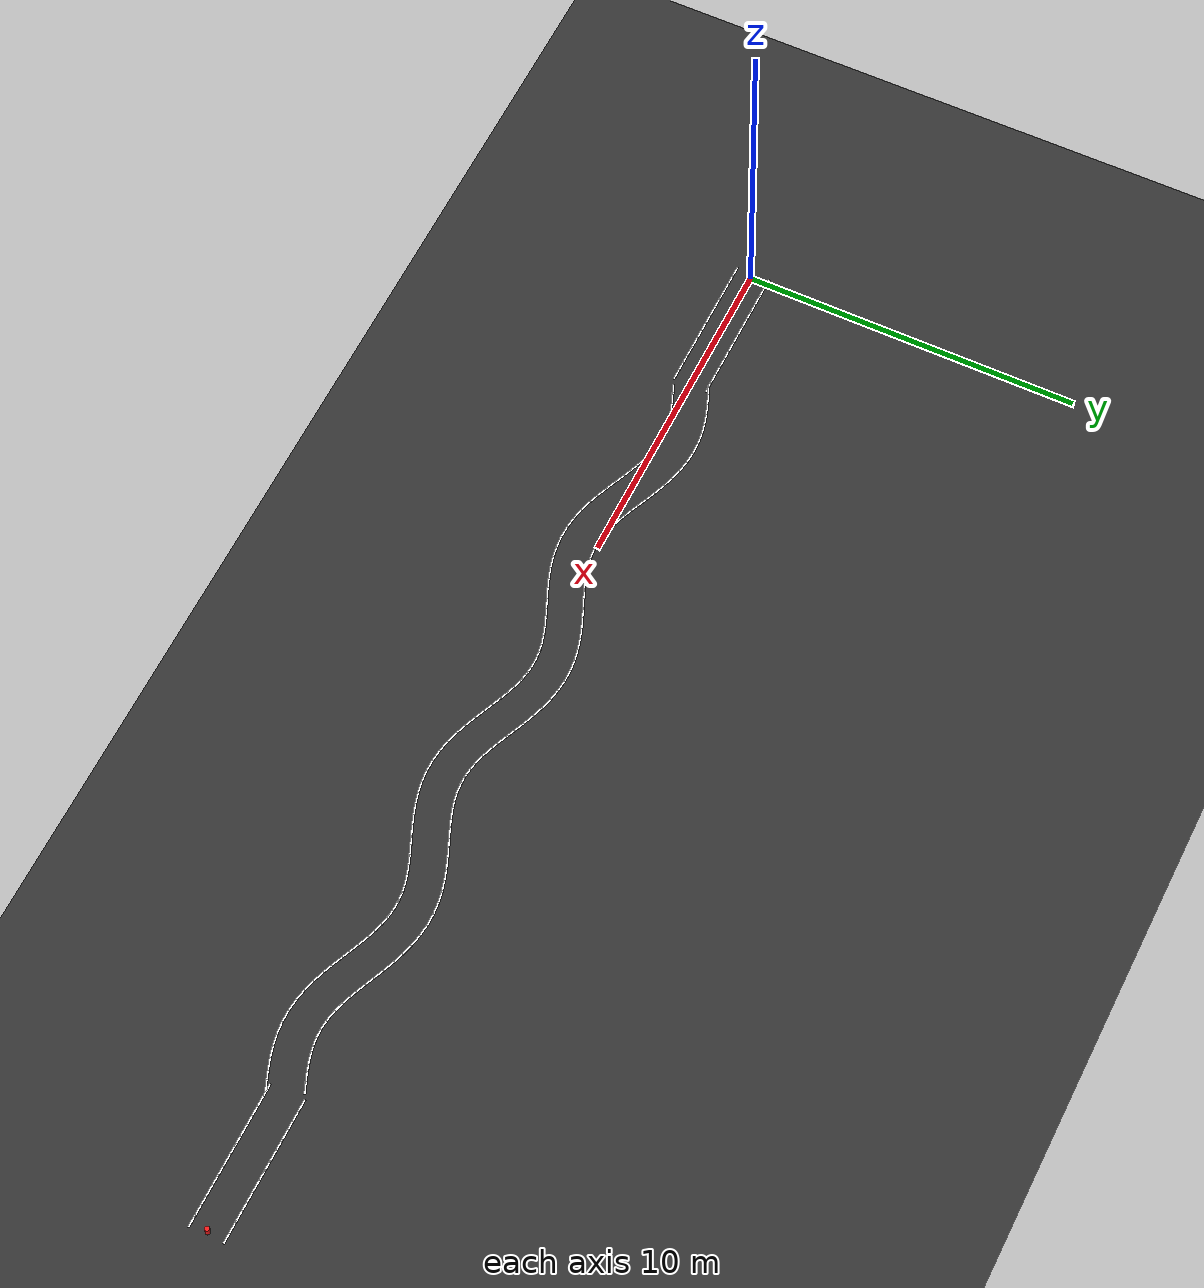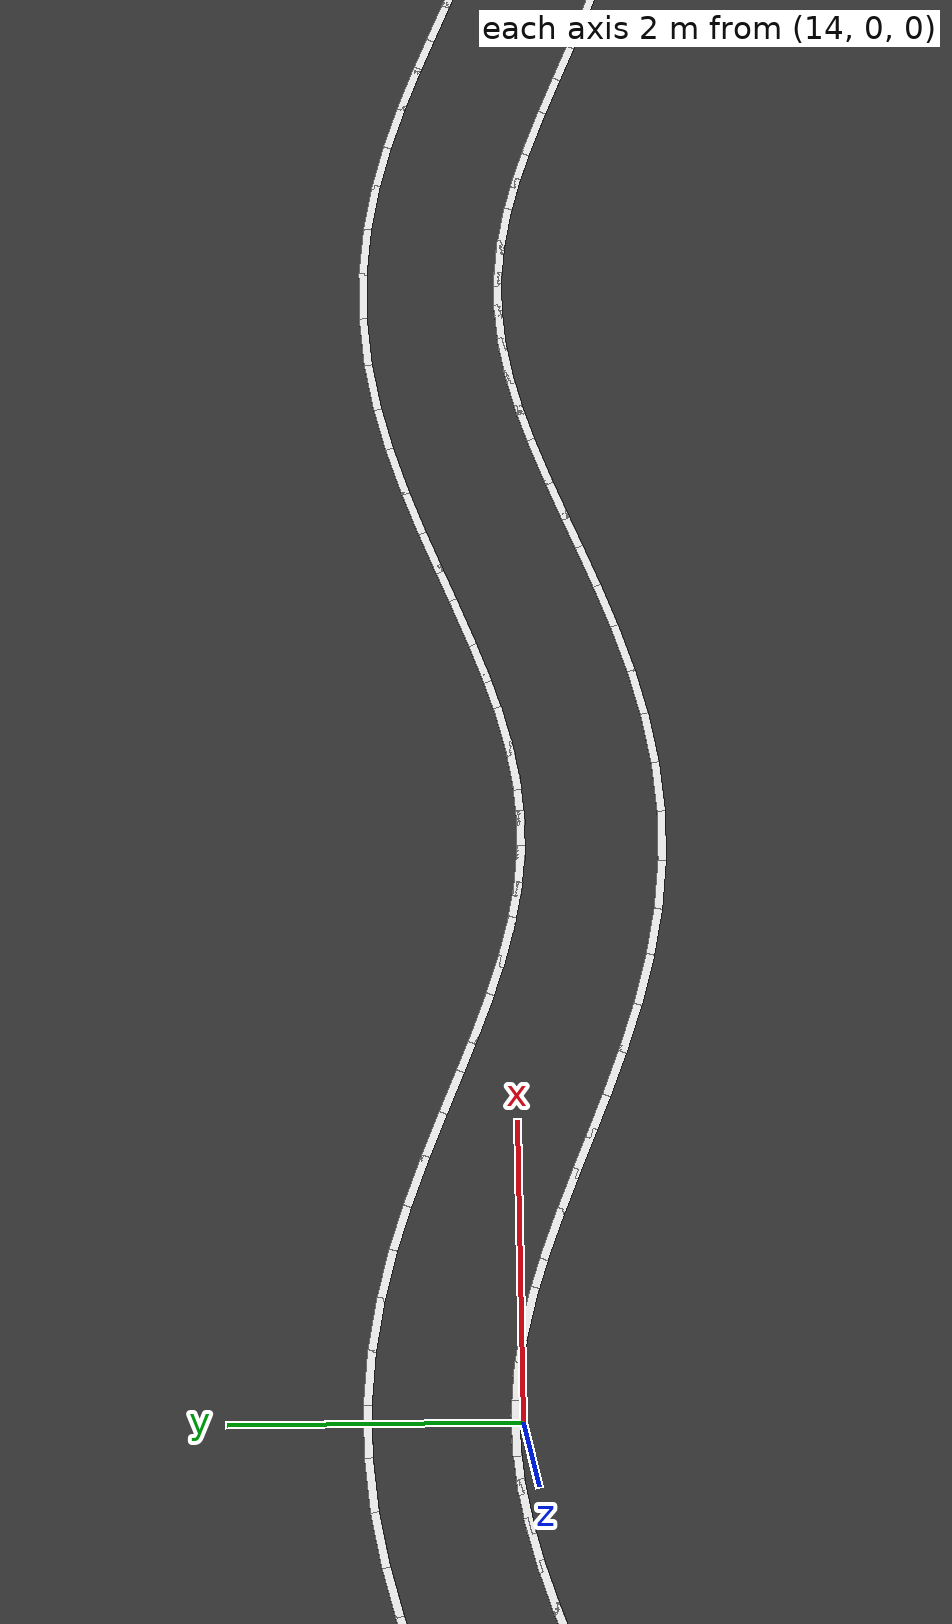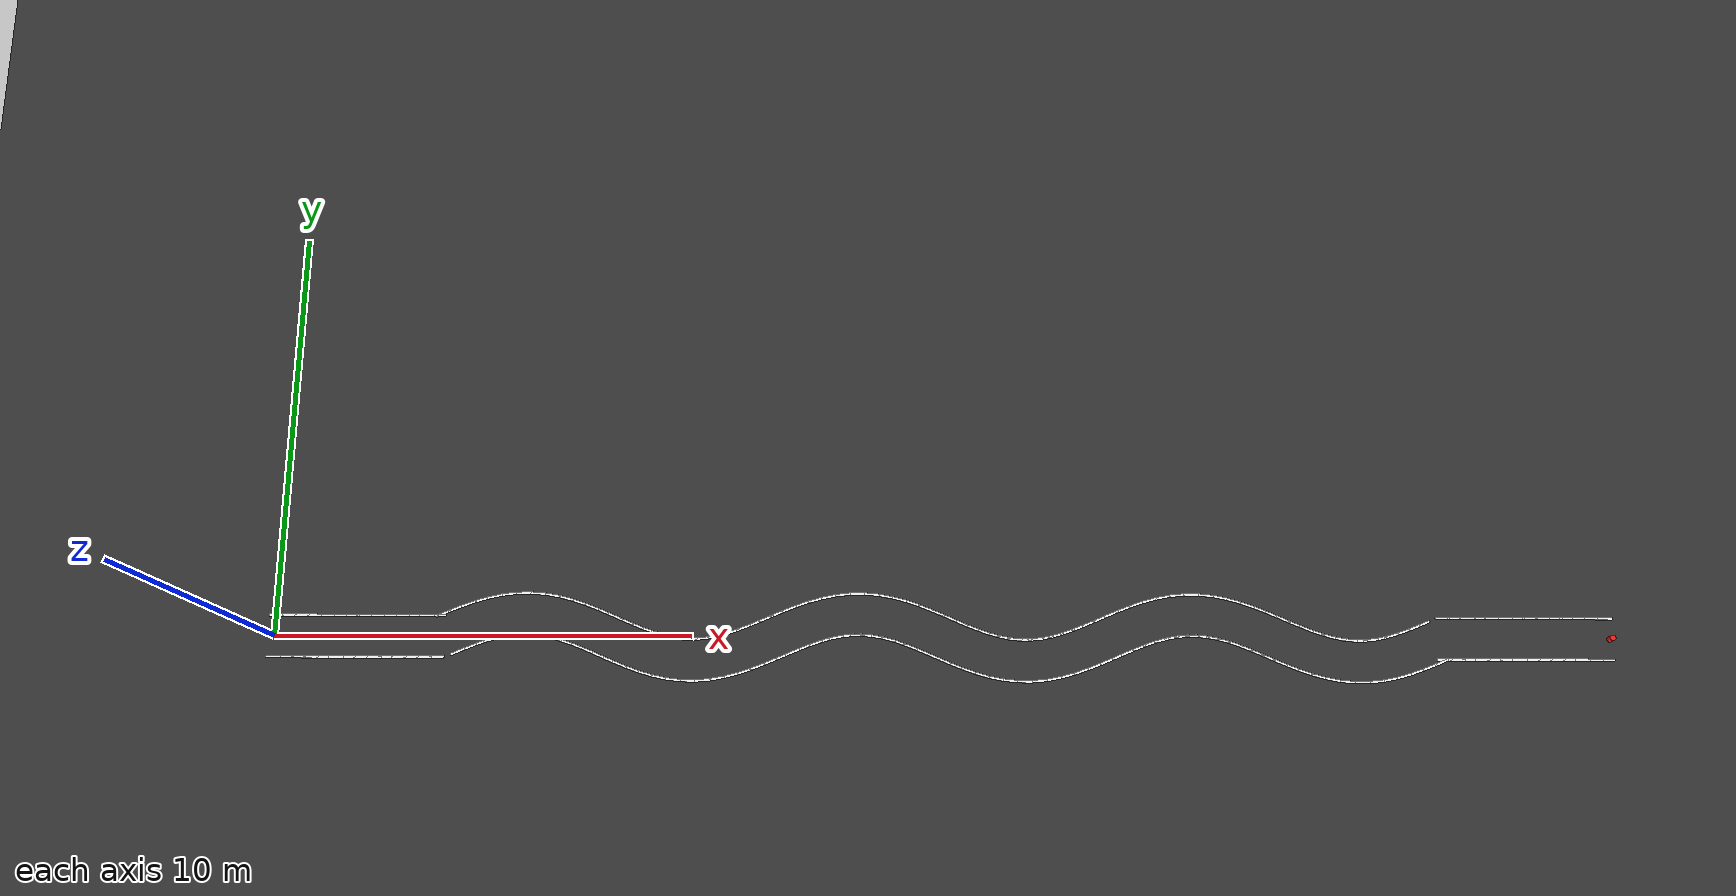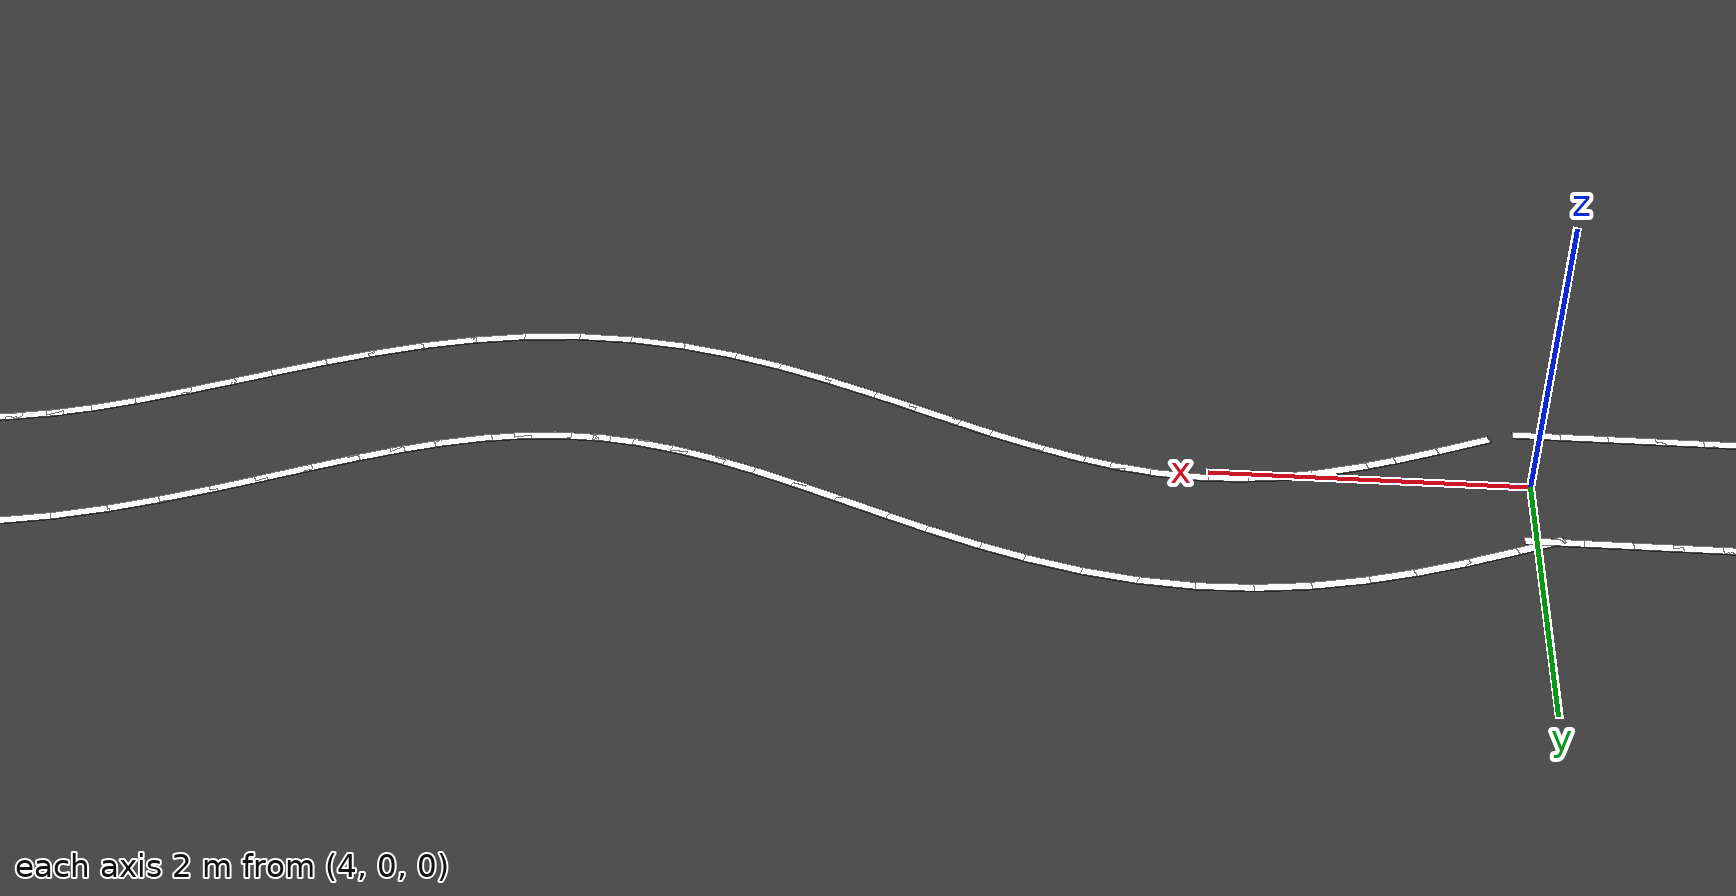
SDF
<?xml version="1.0"?>
<!-- AUTO-GENERATED by scripts/generate_s_curve.py - edit PARAMS there and re-run. -->
<sdf version="1.7">
  <world name="cone_lane">

    <physics type="ode">
      <max_step_size>0.004</max_step_size>
      <real_time_factor>1.0</real_time_factor>
    </physics>

    <plugin filename="libignition-gazebo-physics-system.so"
      name="ignition::gazebo::systems::Physics" />
    <plugin filename="libignition-gazebo-user-commands-system.so"
      name="ignition::gazebo::systems::UserCommands" />
    <plugin filename="libignition-gazebo-scene-broadcaster-system.so"
      name="ignition::gazebo::systems::SceneBroadcaster" />
    <plugin filename="libignition-gazebo-sensors-system.so"
      name="ignition::gazebo::systems::Sensors">
      <render_engine>ogre2</render_engine>
    </plugin>
    <plugin filename="libignition-gazebo-imu-system.so"
      name="ignition::gazebo::systems::Imu" />

    <scene>
      <ambient>0.4 0.4 0.4 1</ambient>
      <background>0.25 0.25 0.25 1</background>
      <shadows>true</shadows>
      <grid>false</grid>
    </scene>

    <light type="directional" name="sun">
      <cast_shadows>true</cast_shadows>
      <pose>0 0 10 0 0 0</pose>
      <diffuse>0.9 0.9 0.9 1</diffuse>
      <specular>0.3 0.3 0.3 1</specular>
      <attenuation>
        <range>1000</range>
        <constant>0.9</constant>
        <linear>0.01</linear>
        <quadratic>0.001</quadratic>
      </attenuation>
      <direction>-0.5 0.1 -0.9</direction>
    </light>

    <!-- DARK asphalt ground so the light-gray markings stand out. -->
    <model name="ground_plane">
      <static>true</static>
      <link name="link">
        <collision name="collision">
          <geometry><plane><normal>0 0 1</normal><size>150 150</size></plane></geometry>
          <surface><friction><ode><mu>1.0</mu></ode></friction></surface>
        </collision>
        <visual name="visual">
          <geometry><plane><normal>0 0 1</normal><size>100 100</size></plane></geometry>
          <material>
            <ambient>0.16 0.16 0.16 1</ambient>
            <diffuse>0.20 0.20 0.20 1</diffuse>
            <specular>0.02 0.02 0.02 1</specular>
          </material>
        </visual>
      </link>
    </model>

    <!-- Left boundary line (light-gray segments) -->
    <model name="line_L001">
      <static>true</static>
      <pose>0.000 0.500 0.0030 0 0 0.0000</pose>
      <link name="link">
        <visual name="v">
          <geometry><box><size>0.360 0.060 0.005</size></box></geometry>
          <material>
            <ambient>0.85 0.85 0.85 1</ambient>
            <diffuse>0.95 0.95 0.95 1</diffuse>
            <specular>0.1 0.1 0.1 1</specular>
          </material>
        </visual>
      </link>
    </model>
    <model name="line_L002">
      <static>true</static>
      <pose>0.300 0.500 0.0030 0 0 0.0000</pose>
      <link name="link">
        <visual name="v">
          <geometry><box><size>0.360 0.060 0.005</size></box></geometry>
          <material>
            <ambient>0.85 0.85 0.85 1</ambient>
            <diffuse>0.95 0.95 0.95 1</diffuse>
            <specular>0.1 0.1 0.1 1</specular>
          </material>
        </visual>
      </link>
    </model>
    <model name="line_L003">
      <static>true</static>
      <pose>0.600 0.500 0.0030 0 0 0.0000</pose>
      <link name="link">
        <visual name="v">
          <geometry><box><size>0.360 0.060 0.005</size></box></geometry>
          <material>
            <ambient>0.85 0.85 0.85 1</ambient>
            <diffuse>0.95 0.95 0.95 1</diffuse>
            <specular>0.1 0.1 0.1 1</specular>
          </material>
        </visual>
      </link>
    </model>
    <model name="line_L004">
      <static>true</static>
      <pose>0.900 0.500 0.0030 0 0 0.0000</pose>
      <link name="link">
        <visual name="v">
          <geometry><box><size>0.360 0.060 0.005</size></box></geometry>
          <material>
            <ambient>0.85 0.85 0.85 1</ambient>
            <diffuse>0.95 0.95 0.95 1</diffuse>
            <specular>0.1 0.1 0.1 1</specular>
          </material>
        </visual>
      </link>
    </model>
    <model name="line_L005">
      <static>true</static>
      <pose>1.200 0.500 0.0030 0 0 0.0000</pose>
      <link name="link">
        <visual name="v">
          <geometry><box><size>0.360 0.060 0.005</size></box></geometry>
          <material>
            <ambient>0.85 0.85 0.85 1</ambient>
            <diffuse>0.95 0.95 0.95 1</diffuse>
            <specular>0.1 0.1 0.1 1</specular>
          </material>
        </visual>
      </link>
    </model>
    <model name="line_L006">
      <static>true</static>
      <pose>1.500 0.500 0.0030 0 0 0.0000</pose>
      <link name="link">
        <visual name="v">
          <geometry><box><size>0.360 0.060 0.005</size></box></geometry>
          <material>
            <ambient>0.85 0.85 0.85 1</ambient>
            <diffuse>0.95 0.95 0.95 1</diffuse>
            <specular>0.1 0.1 0.1 1</specular>
          </material>
        </visual>
      </link>
    </model>
    <model name="line_L007">
      <static>true</static>
      <pose>1.800 0.500 0.0030 0 0 0.0000</pose>
      <link name="link">
        <visual name="v">
          <geometry><box><size>0.360 0.060 0.005</size></box></geometry>
          <material>
            <ambient>0.85 0.85 0.85 1</ambient>
            <diffuse>0.95 0.95 0.95 1</diffuse>
            <specular>0.1 0.1 0.1 1</specular>
          </material>
        </visual>
      </link>
    </model>
    <model name="line_L008">
      <static>true</static>
      <pose>2.100 0.500 0.0030 0 0 0.0000</pose>
      <link name="link">
        <visual name="v">
          <geometry><box><size>0.360 0.060 0.005</size></box></geometry>
          <material>
            <ambient>0.85 0.85 0.85 1</ambient>
            <diffuse>0.95 0.95 0.95 1</diffuse>
            <specular>0.1 0.1 0.1 1</specular>
          </material>
        </visual>
      </link>
    </model>
    <model name="line_L009">
      <static>true</static>
      <pose>2.400 0.500 0.0030 0 0 0.0000</pose>
      <link name="link">
        <visual name="v">
          <geometry><box><size>0.360 0.060 0.005</size></box></geometry>
          <material>
            <ambient>0.85 0.85 0.85 1</ambient>
            <diffuse>0.95 0.95 0.95 1</diffuse>
            <specular>0.1 0.1 0.1 1</specular>
          </material>
        </visual>
      </link>
    </model>
    <model name="line_L010">
      <static>true</static>
      <pose>2.700 0.500 0.0030 0 0 0.0000</pose>
      <link name="link">
        <visual name="v">
          <geometry><box><size>0.360 0.060 0.005</size></box></geometry>
          <material>
            <ambient>0.85 0.85 0.85 1</ambient>
            <diffuse>0.95 0.95 0.95 1</diffuse>
            <specular>0.1 0.1 0.1 1</specular>
          </material>
        </visual>
      </link>
    </model>
    <model name="line_L011">
      <static>true</static>
      <pose>3.000 0.500 0.0030 0 0 0.0000</pose>
      <link name="link">
        <visual name="v">
          <geometry><box><size>0.360 0.060 0.005</size></box></geometry>
          <material>
            <ambient>0.85 0.85 0.85 1</ambient>
            <diffuse>0.95 0.95 0.95 1</diffuse>
            <specular>0.1 0.1 0.1 1</specular>
          </material>
        </visual>
      </link>
    </model>
    <model name="line_L012">
      <static>true</static>
      <pose>3.300 0.500 0.0030 0 0 0.0000</pose>
      <link name="link">
        <visual name="v">
          <geometry><box><size>0.360 0.060 0.005</size></box></geometry>
          <material>
            <ambient>0.85 0.85 0.85 1</ambient>
            <diffuse>0.95 0.95 0.95 1</diffuse>
            <specular>0.1 0.1 0.1 1</specular>
          </material>
        </visual>
      </link>
    </model>
    <model name="line_L013">
      <static>true</static>
      <pose>3.600 0.500 0.0030 0 0 0.0000</pose>
      <link name="link">
        <visual name="v">
          <geometry><box><size>0.360 0.060 0.005</size></box></geometry>
          <material>
            <ambient>0.85 0.85 0.85 1</ambient>
            <diffuse>0.95 0.95 0.95 1</diffuse>
            <specular>0.1 0.1 0.1 1</specular>
          </material>
        </visual>
      </link>
    </model>
    <model name="line_L014">
      <static>true</static>
      <pose>3.900 0.500 0.0030 0 0 0.0000</pose>
      <link name="link">
        <visual name="v">
          <geometry><box><size>0.360 0.060 0.005</size></box></geometry>
          <material>
            <ambient>0.85 0.85 0.85 1</ambient>
            <diffuse>0.95 0.95 0.95 1</diffuse>
            <specular>0.1 0.1 0.1 1</specular>
          </material>
        </visual>
      </link>
    </model>
    <model name="line_L015">
      <static>true</static>
      <pose>4.004 0.546 0.0030 0 0 0.4033</pose>
      <link name="link">
        <visual name="v">
          <geometry><box><size>0.360 0.060 0.005</size></box></geometry>
          <material>
            <ambient>0.85 0.85 0.85 1</ambient>
            <diffuse>0.95 0.95 0.95 1</diffuse>
            <specular>0.1 0.1 0.1 1</specular>
          </material>
        </visual>
      </link>
    </model>
    <model name="line_L016">
      <static>true</static>
      <pose>4.294 0.666 0.0030 0 0 0.3819</pose>
      <link name="link">
        <visual name="v">
          <geometry><box><size>0.360 0.060 0.005</size></box></geometry>
          <material>
            <ambient>0.85 0.85 0.85 1</ambient>
            <diffuse>0.95 0.95 0.95 1</diffuse>
            <specular>0.1 0.1 0.1 1</specular>
          </material>
        </visual>
      </link>
    </model>
    <model name="line_L017">
      <static>true</static>
      <pose>4.592 0.780 0.0030 0 0 0.3431</pose>
      <link name="link">
        <visual name="v">
          <geometry><box><size>0.360 0.060 0.005</size></box></geometry>
          <material>
            <ambient>0.85 0.85 0.85 1</ambient>
            <diffuse>0.95 0.95 0.95 1</diffuse>
            <specular>0.1 0.1 0.1 1</specular>
          </material>
        </visual>
      </link>
    </model>
    <model name="line_L018">
      <static>true</static>
      <pose>4.898 0.880 0.0030 0 0 0.2875</pose>
      <link name="link">
        <visual name="v">
          <geometry><box><size>0.360 0.060 0.005</size></box></geometry>
          <material>
            <ambient>0.85 0.85 0.85 1</ambient>
            <diffuse>0.95 0.95 0.95 1</diffuse>
            <specular>0.1 0.1 0.1 1</specular>
          </material>
        </visual>
      </link>
    </model>
    <model name="line_L019">
      <static>true</static>
      <pose>5.213 0.962 0.0030 0 0 0.2164</pose>
      <link name="link">
        <visual name="v">
          <geometry><box><size>0.360 0.060 0.005</size></box></geometry>
          <material>
            <ambient>0.85 0.85 0.85 1</ambient>
            <diffuse>0.95 0.95 0.95 1</diffuse>
            <specular>0.1 0.1 0.1 1</specular>
          </material>
        </visual>
      </link>
    </model>
    <model name="line_L020">
      <static>true</static>
      <pose>5.557 1.022 0.0030 0 0 0.1263</pose>
      <link name="link">
        <visual name="v">
          <geometry><box><size>0.360 0.060 0.005</size></box></geometry>
          <material>
            <ambient>0.85 0.85 0.85 1</ambient>
            <diffuse>0.95 0.95 0.95 1</diffuse>
            <specular>0.1 0.1 0.1 1</specular>
          </material>
        </visual>
      </link>
    </model>
    <model name="line_L021">
      <static>true</static>
      <pose>5.906 1.049 0.0030 0 0 0.0271</pose>
      <link name="link">
        <visual name="v">
          <geometry><box><size>0.360 0.060 0.005</size></box></geometry>
          <material>
            <ambient>0.85 0.85 0.85 1</ambient>
            <diffuse>0.95 0.95 0.95 1</diffuse>
            <specular>0.1 0.1 0.1 1</specular>
          </material>
        </visual>
      </link>
    </model>
    <model name="line_L022">
      <static>true</static>
      <pose>6.257 1.040 0.0030 0 0 -0.0741</pose>
      <link name="link">
        <visual name="v">
          <geometry><box><size>0.360 0.060 0.005</size></box></geometry>
          <material>
            <ambient>0.85 0.85 0.85 1</ambient>
            <diffuse>0.95 0.95 0.95 1</diffuse>
            <specular>0.1 0.1 0.1 1</specular>
          </material>
        </visual>
      </link>
    </model>
    <model name="line_L023">
      <static>true</static>
      <pose>6.605 0.998 0.0030 0 0 -0.1699</pose>
      <link name="link">
        <visual name="v">
          <geometry><box><size>0.360 0.060 0.005</size></box></geometry>
          <material>
            <ambient>0.85 0.85 0.85 1</ambient>
            <diffuse>0.95 0.95 0.95 1</diffuse>
            <specular>0.1 0.1 0.1 1</specular>
          </material>
        </visual>
      </link>
    </model>
    <model name="line_L024">
      <static>true</static>
      <pose>6.946 0.924 0.0030 0 0 -0.2538</pose>
      <link name="link">
        <visual name="v">
          <geometry><box><size>0.360 0.060 0.005</size></box></geometry>
          <material>
            <ambient>0.85 0.85 0.85 1</ambient>
            <diffuse>0.95 0.95 0.95 1</diffuse>
            <specular>0.1 0.1 0.1 1</specular>
          </material>
        </visual>
      </link>
    </model>
    <model name="line_L025">
      <static>true</static>
      <pose>7.256 0.832 0.0030 0 0 -0.3174</pose>
      <link name="link">
        <visual name="v">
          <geometry><box><size>0.360 0.060 0.005</size></box></geometry>
          <material>
            <ambient>0.85 0.85 0.85 1</ambient>
            <diffuse>0.95 0.95 0.95 1</diffuse>
            <specular>0.1 0.1 0.1 1</specular>
          </material>
        </visual>
      </link>
    </model>
    <model name="line_L026">
      <static>true</static>
      <pose>7.558 0.724 0.0030 0 0 -0.3647</pose>
      <link name="link">
        <visual name="v">
          <geometry><box><size>0.360 0.060 0.005</size></box></geometry>
          <material>
            <ambient>0.85 0.85 0.85 1</ambient>
            <diffuse>0.95 0.95 0.95 1</diffuse>
            <specular>0.1 0.1 0.1 1</specular>
          </material>
        </visual>
      </link>
    </model>
    <model name="line_L027">
      <static>true</static>
      <pose>7.852 0.607 0.0030 0 0 -0.3948</pose>
      <link name="link">
        <visual name="v">
          <geometry><box><size>0.360 0.060 0.005</size></box></geometry>
          <material>
            <ambient>0.85 0.85 0.85 1</ambient>
            <diffuse>0.95 0.95 0.95 1</diffuse>
            <specular>0.1 0.1 0.1 1</specular>
          </material>
        </visual>
      </link>
    </model>
    <model name="line_L028">
      <static>true</static>
      <pose>8.138 0.485 0.0030 0 0 -0.4073</pose>
      <link name="link">
        <visual name="v">
          <geometry><box><size>0.360 0.060 0.005</size></box></geometry>
          <material>
            <ambient>0.85 0.85 0.85 1</ambient>
            <diffuse>0.95 0.95 0.95 1</diffuse>
            <specular>0.1 0.1 0.1 1</specular>
          </material>
        </visual>
      </link>
    </model>
    <model name="line_L029">
      <static>true</static>
      <pose>8.416 0.366 0.0030 0 0 -0.4023</pose>
      <link name="link">
        <visual name="v">
          <geometry><box><size>0.360 0.060 0.005</size></box></geometry>
          <material>
            <ambient>0.85 0.85 0.85 1</ambient>
            <diffuse>0.95 0.95 0.95 1</diffuse>
            <specular>0.1 0.1 0.1 1</specular>
          </material>
        </visual>
      </link>
    </model>
    <model name="line_L030">
      <static>true</static>
      <pose>8.666 0.262 0.0030 0 0 -0.3819</pose>
      <link name="link">
        <visual name="v">
          <geometry><box><size>0.360 0.060 0.005</size></box></geometry>
          <material>
            <ambient>0.85 0.85 0.85 1</ambient>
            <diffuse>0.95 0.95 0.95 1</diffuse>
            <specular>0.1 0.1 0.1 1</specular>
          </material>
        </visual>
      </link>
    </model>
    <model name="line_L031">
      <static>true</static>
      <pose>8.928 0.162 0.0030 0 0 -0.3431</pose>
      <link name="link">
        <visual name="v">
          <geometry><box><size>0.360 0.060 0.005</size></box></geometry>
          <material>
            <ambient>0.85 0.85 0.85 1</ambient>
            <diffuse>0.95 0.95 0.95 1</diffuse>
            <specular>0.1 0.1 0.1 1</specular>
          </material>
        </visual>
      </link>
    </model>
    <model name="line_L032">
      <static>true</static>
      <pose>9.200 0.073 0.0030 0 0 -0.2829</pose>
      <link name="link">
        <visual name="v">
          <geometry><box><size>0.360 0.060 0.005</size></box></geometry>
          <material>
            <ambient>0.85 0.85 0.85 1</ambient>
            <diffuse>0.95 0.95 0.95 1</diffuse>
            <specular>0.1 0.1 0.1 1</specular>
          </material>
        </visual>
      </link>
    </model>
    <model name="line_L033">
      <static>true</static>
      <pose>9.445 0.011 0.0030 0 0 -0.2108</pose>
      <link name="link">
        <visual name="v">
          <geometry><box><size>0.360 0.060 0.005</size></box></geometry>
          <material>
            <ambient>0.85 0.85 0.85 1</ambient>
            <diffuse>0.95 0.95 0.95 1</diffuse>
            <specular>0.1 0.1 0.1 1</specular>
          </material>
        </visual>
      </link>
    </model>
    <model name="line_L034">
      <static>true</static>
      <pose>9.700 -0.032 0.0030 0 0 -0.1199</pose>
      <link name="link">
        <visual name="v">
          <geometry><box><size>0.360 0.060 0.005</size></box></geometry>
          <material>
            <ambient>0.85 0.85 0.85 1</ambient>
            <diffuse>0.95 0.95 0.95 1</diffuse>
            <specular>0.1 0.1 0.1 1</specular>
          </material>
        </visual>
      </link>
    </model>
    <model name="line_L035">
      <static>true</static>
      <pose>9.950 -0.049 0.0030 0 0 -0.0203</pose>
      <link name="link">
        <visual name="v">
          <geometry><box><size>0.360 0.060 0.005</size></box></geometry>
          <material>
            <ambient>0.85 0.85 0.85 1</ambient>
            <diffuse>0.95 0.95 0.95 1</diffuse>
            <specular>0.1 0.1 0.1 1</specular>
          </material>
        </visual>
      </link>
    </model>
    <model name="line_L036">
      <static>true</static>
      <pose>10.200 -0.042 0.0030 0 0 0.0808</pose>
      <link name="link">
        <visual name="v">
          <geometry><box><size>0.360 0.060 0.005</size></box></geometry>
          <material>
            <ambient>0.85 0.85 0.85 1</ambient>
            <diffuse>0.95 0.95 0.95 1</diffuse>
            <specular>0.1 0.1 0.1 1</specular>
          </material>
        </visual>
      </link>
    </model>
    <model name="line_L037">
      <static>true</static>
      <pose>10.452 -0.009 0.0030 0 0 0.1759</pose>
      <link name="link">
        <visual name="v">
          <geometry><box><size>0.360 0.060 0.005</size></box></geometry>
          <material>
            <ambient>0.85 0.85 0.85 1</ambient>
            <diffuse>0.95 0.95 0.95 1</diffuse>
            <specular>0.1 0.1 0.1 1</specular>
          </material>
        </visual>
      </link>
    </model>
    <model name="line_L038">
      <static>true</static>
      <pose>10.694 0.044 0.0030 0 0 0.2538</pose>
      <link name="link">
        <visual name="v">
          <geometry><box><size>0.360 0.060 0.005</size></box></geometry>
          <material>
            <ambient>0.85 0.85 0.85 1</ambient>
            <diffuse>0.95 0.95 0.95 1</diffuse>
            <specular>0.1 0.1 0.1 1</specular>
          </material>
        </visual>
      </link>
    </model>
    <model name="line_L039">
      <static>true</static>
      <pose>10.962 0.124 0.0030 0 0 0.3213</pose>
      <link name="link">
        <visual name="v">
          <geometry><box><size>0.360 0.060 0.005</size></box></geometry>
          <material>
            <ambient>0.85 0.85 0.85 1</ambient>
            <diffuse>0.95 0.95 0.95 1</diffuse>
            <specular>0.1 0.1 0.1 1</specular>
          </material>
        </visual>
      </link>
    </model>
    <model name="line_L040">
      <static>true</static>
      <pose>11.220 0.217 0.0030 0 0 0.3674</pose>
      <link name="link">
        <visual name="v">
          <geometry><box><size>0.360 0.060 0.005</size></box></geometry>
          <material>
            <ambient>0.85 0.85 0.85 1</ambient>
            <diffuse>0.95 0.95 0.95 1</diffuse>
            <specular>0.1 0.1 0.1 1</specular>
          </material>
        </visual>
      </link>
    </model>
    <model name="line_L041">
      <static>true</static>
      <pose>11.487 0.324 0.0030 0 0 0.3963</pose>
      <link name="link">
        <visual name="v">
          <geometry><box><size>0.360 0.060 0.005</size></box></geometry>
          <material>
            <ambient>0.85 0.85 0.85 1</ambient>
            <diffuse>0.95 0.95 0.95 1</diffuse>
            <specular>0.1 0.1 0.1 1</specular>
          </material>
        </visual>
      </link>
    </model>
    <model name="line_L042">
      <static>true</static>
      <pose>11.762 0.442 0.0030 0 0 0.4076</pose>
      <link name="link">
        <visual name="v">
          <geometry><box><size>0.360 0.060 0.005</size></box></geometry>
          <material>
            <ambient>0.85 0.85 0.85 1</ambient>
            <diffuse>0.95 0.95 0.95 1</diffuse>
            <specular>0.1 0.1 0.1 1</specular>
          </material>
        </visual>
      </link>
    </model>
    <model name="line_L043">
      <static>true</static>
      <pose>12.024 0.555 0.0030 0 0 0.4023</pose>
      <link name="link">
        <visual name="v">
          <geometry><box><size>0.360 0.060 0.005</size></box></geometry>
          <material>
            <ambient>0.85 0.85 0.85 1</ambient>
            <diffuse>0.95 0.95 0.95 1</diffuse>
            <specular>0.1 0.1 0.1 1</specular>
          </material>
        </visual>
      </link>
    </model>
    <model name="line_L044">
      <static>true</static>
      <pose>12.315 0.675 0.0030 0 0 0.3797</pose>
      <link name="link">
        <visual name="v">
          <geometry><box><size>0.360 0.060 0.005</size></box></geometry>
          <material>
            <ambient>0.85 0.85 0.85 1</ambient>
            <diffuse>0.95 0.95 0.95 1</diffuse>
            <specular>0.1 0.1 0.1 1</specular>
          </material>
        </visual>
      </link>
    </model>
    <model name="line_L045">
      <static>true</static>
      <pose>12.613 0.788 0.0030 0 0 0.3397</pose>
      <link name="link">
        <visual name="v">
          <geometry><box><size>0.360 0.060 0.005</size></box></geometry>
          <material>
            <ambient>0.85 0.85 0.85 1</ambient>
            <diffuse>0.95 0.95 0.95 1</diffuse>
            <specular>0.1 0.1 0.1 1</specular>
          </material>
        </visual>
      </link>
    </model>
    <model name="line_L046">
      <static>true</static>
      <pose>12.943 0.893 0.0030 0 0 0.2782</pose>
      <link name="link">
        <visual name="v">
          <geometry><box><size>0.360 0.060 0.005</size></box></geometry>
          <material>
            <ambient>0.85 0.85 0.85 1</ambient>
            <diffuse>0.95 0.95 0.95 1</diffuse>
            <specular>0.1 0.1 0.1 1</specular>
          </material>
        </visual>
      </link>
    </model>
    <model name="line_L047">
      <static>true</static>
      <pose>13.258 0.971 0.0030 0 0 0.2052</pose>
      <link name="link">
        <visual name="v">
          <geometry><box><size>0.360 0.060 0.005</size></box></geometry>
          <material>
            <ambient>0.85 0.85 0.85 1</ambient>
            <diffuse>0.95 0.95 0.95 1</diffuse>
            <specular>0.1 0.1 0.1 1</specular>
          </material>
        </visual>
      </link>
    </model>
    <model name="line_L048">
      <static>true</static>
      <pose>13.603 1.027 0.0030 0 0 0.1135</pose>
      <link name="link">
        <visual name="v">
          <geometry><box><size>0.360 0.060 0.005</size></box></geometry>
          <material>
            <ambient>0.85 0.85 0.85 1</ambient>
            <diffuse>0.95 0.95 0.95 1</diffuse>
            <specular>0.1 0.1 0.1 1</specular>
          </material>
        </visual>
      </link>
    </model>
    <model name="line_L049">
      <static>true</static>
      <pose>13.953 1.050 0.0030 0 0 0.0136</pose>
      <link name="link">
        <visual name="v">
          <geometry><box><size>0.360 0.060 0.005</size></box></geometry>
          <material>
            <ambient>0.85 0.85 0.85 1</ambient>
            <diffuse>0.95 0.95 0.95 1</diffuse>
            <specular>0.1 0.1 0.1 1</specular>
          </material>
        </visual>
      </link>
    </model>
    <model name="line_L050">
      <static>true</static>
      <pose>14.304 1.037 0.0030 0 0 -0.0874</pose>
      <link name="link">
        <visual name="v">
          <geometry><box><size>0.360 0.060 0.005</size></box></geometry>
          <material>
            <ambient>0.85 0.85 0.85 1</ambient>
            <diffuse>0.95 0.95 0.95 1</diffuse>
            <specular>0.1 0.1 0.1 1</specular>
          </material>
        </visual>
      </link>
    </model>
    <model name="line_L051">
      <static>true</static>
      <pose>14.650 0.989 0.0030 0 0 -0.1819</pose>
      <link name="link">
        <visual name="v">
          <geometry><box><size>0.360 0.060 0.005</size></box></geometry>
          <material>
            <ambient>0.85 0.85 0.85 1</ambient>
            <diffuse>0.95 0.95 0.95 1</diffuse>
            <specular>0.1 0.1 0.1 1</specular>
          </material>
        </visual>
      </link>
    </model>
    <model name="line_L052">
      <static>true</static>
      <pose>14.968 0.918 0.0030 0 0 -0.2588</pose>
      <link name="link">
        <visual name="v">
          <geometry><box><size>0.360 0.060 0.005</size></box></geometry>
          <material>
            <ambient>0.85 0.85 0.85 1</ambient>
            <diffuse>0.95 0.95 0.95 1</diffuse>
            <specular>0.1 0.1 0.1 1</specular>
          </material>
        </visual>
      </link>
    </model>
    <model name="line_L053">
      <static>true</static>
      <pose>15.300 0.818 0.0030 0 0 -0.3251</pose>
      <link name="link">
        <visual name="v">
          <geometry><box><size>0.360 0.060 0.005</size></box></geometry>
          <material>
            <ambient>0.85 0.85 0.85 1</ambient>
            <diffuse>0.95 0.95 0.95 1</diffuse>
            <specular>0.1 0.1 0.1 1</specular>
          </material>
        </visual>
      </link>
    </model>
    <model name="line_L054">
      <static>true</static>
      <pose>15.601 0.708 0.0030 0 0 -0.3700</pose>
      <link name="link">
        <visual name="v">
          <geometry><box><size>0.360 0.060 0.005</size></box></geometry>
          <material>
            <ambient>0.85 0.85 0.85 1</ambient>
            <diffuse>0.95 0.95 0.95 1</diffuse>
            <specular>0.1 0.1 0.1 1</specular>
          </material>
        </visual>
      </link>
    </model>
    <model name="line_L055">
      <static>true</static>
      <pose>15.894 0.589 0.0030 0 0 -0.3976</pose>
      <link name="link">
        <visual name="v">
          <geometry><box><size>0.360 0.060 0.005</size></box></geometry>
          <material>
            <ambient>0.85 0.85 0.85 1</ambient>
            <diffuse>0.95 0.95 0.95 1</diffuse>
            <specular>0.1 0.1 0.1 1</specular>
          </material>
        </visual>
      </link>
    </model>
    <model name="line_L056">
      <static>true</static>
      <pose>16.178 0.468 0.0030 0 0 -0.4077</pose>
      <link name="link">
        <visual name="v">
          <geometry><box><size>0.360 0.060 0.005</size></box></geometry>
          <material>
            <ambient>0.85 0.85 0.85 1</ambient>
            <diffuse>0.95 0.95 0.95 1</diffuse>
            <specular>0.1 0.1 0.1 1</specular>
          </material>
        </visual>
      </link>
    </model>
    <model name="line_L057">
      <static>true</static>
      <pose>16.435 0.357 0.0030 0 0 -0.4013</pose>
      <link name="link">
        <visual name="v">
          <geometry><box><size>0.360 0.060 0.005</size></box></geometry>
          <material>
            <ambient>0.85 0.85 0.85 1</ambient>
            <diffuse>0.95 0.95 0.95 1</diffuse>
            <specular>0.1 0.1 0.1 1</specular>
          </material>
        </visual>
      </link>
    </model>
    <model name="line_L058">
      <static>true</static>
      <pose>16.704 0.246 0.0030 0 0 -0.3774</pose>
      <link name="link">
        <visual name="v">
          <geometry><box><size>0.360 0.060 0.005</size></box></geometry>
          <material>
            <ambient>0.85 0.85 0.85 1</ambient>
            <diffuse>0.95 0.95 0.95 1</diffuse>
            <specular>0.1 0.1 0.1 1</specular>
          </material>
        </visual>
      </link>
    </model>
    <model name="line_L059">
      <static>true</static>
      <pose>16.965 0.149 0.0030 0 0 -0.3362</pose>
      <link name="link">
        <visual name="v">
          <geometry><box><size>0.360 0.060 0.005</size></box></geometry>
          <material>
            <ambient>0.85 0.85 0.85 1</ambient>
            <diffuse>0.95 0.95 0.95 1</diffuse>
            <specular>0.1 0.1 0.1 1</specular>
          </material>
        </visual>
      </link>
    </model>
    <model name="line_L060">
      <static>true</static>
      <pose>17.235 0.063 0.0030 0 0 -0.2735</pose>
      <link name="link">
        <visual name="v">
          <geometry><box><size>0.360 0.060 0.005</size></box></geometry>
          <material>
            <ambient>0.85 0.85 0.85 1</ambient>
            <diffuse>0.95 0.95 0.95 1</diffuse>
            <specular>0.1 0.1 0.1 1</specular>
          </material>
        </visual>
      </link>
    </model>
    <model name="line_L061">
      <static>true</static>
      <pose>17.479 0.004 0.0030 0 0 -0.1994</pose>
      <link name="link">
        <visual name="v">
          <geometry><box><size>0.360 0.060 0.005</size></box></geometry>
          <material>
            <ambient>0.85 0.85 0.85 1</ambient>
            <diffuse>0.95 0.95 0.95 1</diffuse>
            <specular>0.1 0.1 0.1 1</specular>
          </material>
        </visual>
      </link>
    </model>
    <model name="line_L062">
      <static>true</static>
      <pose>17.733 -0.036 0.0030 0 0 -0.1070</pose>
      <link name="link">
        <visual name="v">
          <geometry><box><size>0.360 0.060 0.005</size></box></geometry>
          <material>
            <ambient>0.85 0.85 0.85 1</ambient>
            <diffuse>0.95 0.95 0.95 1</diffuse>
            <specular>0.1 0.1 0.1 1</specular>
          </material>
        </visual>
      </link>
    </model>
    <model name="line_L063">
      <static>true</static>
      <pose>17.983 -0.050 0.0030 0 0 -0.0068</pose>
      <link name="link">
        <visual name="v">
          <geometry><box><size>0.360 0.060 0.005</size></box></geometry>
          <material>
            <ambient>0.85 0.85 0.85 1</ambient>
            <diffuse>0.95 0.95 0.95 1</diffuse>
            <specular>0.1 0.1 0.1 1</specular>
          </material>
        </visual>
      </link>
    </model>
    <model name="line_L064">
      <static>true</static>
      <pose>18.233 -0.039 0.0030 0 0 0.0939</pose>
      <link name="link">
        <visual name="v">
          <geometry><box><size>0.360 0.060 0.005</size></box></geometry>
          <material>
            <ambient>0.85 0.85 0.85 1</ambient>
            <diffuse>0.95 0.95 0.95 1</diffuse>
            <specular>0.1 0.1 0.1 1</specular>
          </material>
        </visual>
      </link>
    </model>
    <model name="line_L065">
      <static>true</static>
      <pose>18.487 -0.003 0.0030 0 0 0.1878</pose>
      <link name="link">
        <visual name="v">
          <geometry><box><size>0.360 0.060 0.005</size></box></geometry>
          <material>
            <ambient>0.85 0.85 0.85 1</ambient>
            <diffuse>0.95 0.95 0.95 1</diffuse>
            <specular>0.1 0.1 0.1 1</specular>
          </material>
        </visual>
      </link>
    </model>
    <model name="line_L066">
      <static>true</static>
      <pose>18.730 0.053 0.0030 0 0 0.2638</pose>
      <link name="link">
        <visual name="v">
          <geometry><box><size>0.360 0.060 0.005</size></box></geometry>
          <material>
            <ambient>0.85 0.85 0.85 1</ambient>
            <diffuse>0.95 0.95 0.95 1</diffuse>
            <specular>0.1 0.1 0.1 1</specular>
          </material>
        </visual>
      </link>
    </model>
    <model name="line_L067">
      <static>true</static>
      <pose>18.998 0.136 0.0030 0 0 0.3289</pose>
      <link name="link">
        <visual name="v">
          <geometry><box><size>0.360 0.060 0.005</size></box></geometry>
          <material>
            <ambient>0.85 0.85 0.85 1</ambient>
            <diffuse>0.95 0.95 0.95 1</diffuse>
            <specular>0.1 0.1 0.1 1</specular>
          </material>
        </visual>
      </link>
    </model>
    <model name="line_L068">
      <static>true</static>
      <pose>19.258 0.232 0.0030 0 0 0.3726</pose>
      <link name="link">
        <visual name="v">
          <geometry><box><size>0.360 0.060 0.005</size></box></geometry>
          <material>
            <ambient>0.85 0.85 0.85 1</ambient>
            <diffuse>0.95 0.95 0.95 1</diffuse>
            <specular>0.1 0.1 0.1 1</specular>
          </material>
        </visual>
      </link>
    </model>
    <model name="line_L069">
      <static>true</static>
      <pose>19.526 0.341 0.0030 0 0 0.3989</pose>
      <link name="link">
        <visual name="v">
          <geometry><box><size>0.360 0.060 0.005</size></box></geometry>
          <material>
            <ambient>0.85 0.85 0.85 1</ambient>
            <diffuse>0.95 0.95 0.95 1</diffuse>
            <specular>0.1 0.1 0.1 1</specular>
          </material>
        </visual>
      </link>
    </model>
    <model name="line_L070">
      <static>true</static>
      <pose>19.782 0.450 0.0030 0 0 0.4077</pose>
      <link name="link">
        <visual name="v">
          <geometry><box><size>0.360 0.060 0.005</size></box></geometry>
          <material>
            <ambient>0.85 0.85 0.85 1</ambient>
            <diffuse>0.95 0.95 0.95 1</diffuse>
            <specular>0.1 0.1 0.1 1</specular>
          </material>
        </visual>
      </link>
    </model>
    <model name="line_L071">
      <static>true</static>
      <pose>20.065 0.572 0.0030 0 0 0.4002</pose>
      <link name="link">
        <visual name="v">
          <geometry><box><size>0.360 0.060 0.005</size></box></geometry>
          <material>
            <ambient>0.85 0.85 0.85 1</ambient>
            <diffuse>0.95 0.95 0.95 1</diffuse>
            <specular>0.1 0.1 0.1 1</specular>
          </material>
        </visual>
      </link>
    </model>
    <model name="line_L072">
      <static>true</static>
      <pose>20.357 0.692 0.0030 0 0 0.3750</pose>
      <link name="link">
        <visual name="v">
          <geometry><box><size>0.360 0.060 0.005</size></box></geometry>
          <material>
            <ambient>0.85 0.85 0.85 1</ambient>
            <diffuse>0.95 0.95 0.95 1</diffuse>
            <specular>0.1 0.1 0.1 1</specular>
          </material>
        </visual>
      </link>
    </model>
    <model name="line_L073">
      <static>true</static>
      <pose>20.657 0.803 0.0030 0 0 0.3326</pose>
      <link name="link">
        <visual name="v">
          <geometry><box><size>0.360 0.060 0.005</size></box></geometry>
          <material>
            <ambient>0.85 0.85 0.85 1</ambient>
            <diffuse>0.95 0.95 0.95 1</diffuse>
            <specular>0.1 0.1 0.1 1</specular>
          </material>
        </visual>
      </link>
    </model>
    <model name="line_L074">
      <static>true</static>
      <pose>20.987 0.906 0.0030 0 0 0.2687</pose>
      <link name="link">
        <visual name="v">
          <geometry><box><size>0.360 0.060 0.005</size></box></geometry>
          <material>
            <ambient>0.85 0.85 0.85 1</ambient>
            <diffuse>0.95 0.95 0.95 1</diffuse>
            <specular>0.1 0.1 0.1 1</specular>
          </material>
        </visual>
      </link>
    </model>
    <model name="line_L075">
      <static>true</static>
      <pose>21.304 0.981 0.0030 0 0 0.1936</pose>
      <link name="link">
        <visual name="v">
          <geometry><box><size>0.360 0.060 0.005</size></box></geometry>
          <material>
            <ambient>0.85 0.85 0.85 1</ambient>
            <diffuse>0.95 0.95 0.95 1</diffuse>
            <specular>0.1 0.1 0.1 1</specular>
          </material>
        </visual>
      </link>
    </model>
    <model name="line_L076">
      <static>true</static>
      <pose>21.650 1.032 0.0030 0 0 0.1005</pose>
      <link name="link">
        <visual name="v">
          <geometry><box><size>0.360 0.060 0.005</size></box></geometry>
          <material>
            <ambient>0.85 0.85 0.85 1</ambient>
            <diffuse>0.95 0.95 0.95 1</diffuse>
            <specular>0.1 0.1 0.1 1</specular>
          </material>
        </visual>
      </link>
    </model>
    <model name="line_L077">
      <static>true</static>
      <pose>22.000 1.050 0.0030 0 0 0.0000</pose>
      <link name="link">
        <visual name="v">
          <geometry><box><size>0.360 0.060 0.005</size></box></geometry>
          <material>
            <ambient>0.85 0.85 0.85 1</ambient>
            <diffuse>0.95 0.95 0.95 1</diffuse>
            <specular>0.1 0.1 0.1 1</specular>
          </material>
        </visual>
      </link>
    </model>
    <model name="line_L078">
      <static>true</static>
      <pose>22.350 1.032 0.0030 0 0 -0.1005</pose>
      <link name="link">
        <visual name="v">
          <geometry><box><size>0.360 0.060 0.005</size></box></geometry>
          <material>
            <ambient>0.85 0.85 0.85 1</ambient>
            <diffuse>0.95 0.95 0.95 1</diffuse>
            <specular>0.1 0.1 0.1 1</specular>
          </material>
        </visual>
      </link>
    </model>
    <model name="line_L079">
      <static>true</static>
      <pose>22.696 0.981 0.0030 0 0 -0.1936</pose>
      <link name="link">
        <visual name="v">
          <geometry><box><size>0.360 0.060 0.005</size></box></geometry>
          <material>
            <ambient>0.85 0.85 0.85 1</ambient>
            <diffuse>0.95 0.95 0.95 1</diffuse>
            <specular>0.1 0.1 0.1 1</specular>
          </material>
        </visual>
      </link>
    </model>
    <model name="line_L080">
      <static>true</static>
      <pose>23.013 0.906 0.0030 0 0 -0.2687</pose>
      <link name="link">
        <visual name="v">
          <geometry><box><size>0.360 0.060 0.005</size></box></geometry>
          <material>
            <ambient>0.85 0.85 0.85 1</ambient>
            <diffuse>0.95 0.95 0.95 1</diffuse>
            <specular>0.1 0.1 0.1 1</specular>
          </material>
        </visual>
      </link>
    </model>
    <model name="line_L081">
      <static>true</static>
      <pose>23.343 0.803 0.0030 0 0 -0.3326</pose>
      <link name="link">
        <visual name="v">
          <geometry><box><size>0.360 0.060 0.005</size></box></geometry>
          <material>
            <ambient>0.85 0.85 0.85 1</ambient>
            <diffuse>0.95 0.95 0.95 1</diffuse>
            <specular>0.1 0.1 0.1 1</specular>
          </material>
        </visual>
      </link>
    </model>
    <model name="line_L082">
      <static>true</static>
      <pose>23.643 0.692 0.0030 0 0 -0.3750</pose>
      <link name="link">
        <visual name="v">
          <geometry><box><size>0.360 0.060 0.005</size></box></geometry>
          <material>
            <ambient>0.85 0.85 0.85 1</ambient>
            <diffuse>0.95 0.95 0.95 1</diffuse>
            <specular>0.1 0.1 0.1 1</specular>
          </material>
        </visual>
      </link>
    </model>
    <model name="line_L083">
      <static>true</static>
      <pose>23.935 0.572 0.0030 0 0 -0.4002</pose>
      <link name="link">
        <visual name="v">
          <geometry><box><size>0.360 0.060 0.005</size></box></geometry>
          <material>
            <ambient>0.85 0.85 0.85 1</ambient>
            <diffuse>0.95 0.95 0.95 1</diffuse>
            <specular>0.1 0.1 0.1 1</specular>
          </material>
        </visual>
      </link>
    </model>
    <model name="line_L084">
      <static>true</static>
      <pose>24.198 0.459 0.0030 0 0 -0.4077</pose>
      <link name="link">
        <visual name="v">
          <geometry><box><size>0.360 0.060 0.005</size></box></geometry>
          <material>
            <ambient>0.85 0.85 0.85 1</ambient>
            <diffuse>0.95 0.95 0.95 1</diffuse>
            <specular>0.1 0.1 0.1 1</specular>
          </material>
        </visual>
      </link>
    </model>
    <model name="line_L085">
      <static>true</static>
      <pose>24.474 0.341 0.0030 0 0 -0.3989</pose>
      <link name="link">
        <visual name="v">
          <geometry><box><size>0.360 0.060 0.005</size></box></geometry>
          <material>
            <ambient>0.85 0.85 0.85 1</ambient>
            <diffuse>0.95 0.95 0.95 1</diffuse>
            <specular>0.1 0.1 0.1 1</specular>
          </material>
        </visual>
      </link>
    </model>
    <model name="line_L086">
      <static>true</static>
      <pose>24.742 0.232 0.0030 0 0 -0.3726</pose>
      <link name="link">
        <visual name="v">
          <geometry><box><size>0.360 0.060 0.005</size></box></geometry>
          <material>
            <ambient>0.85 0.85 0.85 1</ambient>
            <diffuse>0.95 0.95 0.95 1</diffuse>
            <specular>0.1 0.1 0.1 1</specular>
          </material>
        </visual>
      </link>
    </model>
    <model name="line_L087">
      <static>true</static>
      <pose>25.002 0.136 0.0030 0 0 -0.3289</pose>
      <link name="link">
        <visual name="v">
          <geometry><box><size>0.360 0.060 0.005</size></box></geometry>
          <material>
            <ambient>0.85 0.85 0.85 1</ambient>
            <diffuse>0.95 0.95 0.95 1</diffuse>
            <specular>0.1 0.1 0.1 1</specular>
          </material>
        </visual>
      </link>
    </model>
    <model name="line_L088">
      <static>true</static>
      <pose>25.253 0.058 0.0030 0 0 -0.2687</pose>
      <link name="link">
        <visual name="v">
          <geometry><box><size>0.360 0.060 0.005</size></box></geometry>
          <material>
            <ambient>0.85 0.85 0.85 1</ambient>
            <diffuse>0.95 0.95 0.95 1</diffuse>
            <specular>0.1 0.1 0.1 1</specular>
          </material>
        </visual>
      </link>
    </model>
    <model name="line_L089">
      <static>true</static>
      <pose>25.513 -0.003 0.0030 0 0 -0.1878</pose>
      <link name="link">
        <visual name="v">
          <geometry><box><size>0.360 0.060 0.005</size></box></geometry>
          <material>
            <ambient>0.85 0.85 0.85 1</ambient>
            <diffuse>0.95 0.95 0.95 1</diffuse>
            <specular>0.1 0.1 0.1 1</specular>
          </material>
        </visual>
      </link>
    </model>
    <model name="line_L090">
      <static>true</static>
      <pose>25.767 -0.039 0.0030 0 0 -0.0939</pose>
      <link name="link">
        <visual name="v">
          <geometry><box><size>0.360 0.060 0.005</size></box></geometry>
          <material>
            <ambient>0.85 0.85 0.85 1</ambient>
            <diffuse>0.95 0.95 0.95 1</diffuse>
            <specular>0.1 0.1 0.1 1</specular>
          </material>
        </visual>
      </link>
    </model>
    <model name="line_L091">
      <static>true</static>
      <pose>26.017 -0.050 0.0030 0 0 0.0068</pose>
      <link name="link">
        <visual name="v">
          <geometry><box><size>0.360 0.060 0.005</size></box></geometry>
          <material>
            <ambient>0.85 0.85 0.85 1</ambient>
            <diffuse>0.95 0.95 0.95 1</diffuse>
            <specular>0.1 0.1 0.1 1</specular>
          </material>
        </visual>
      </link>
    </model>
    <model name="line_L092">
      <static>true</static>
      <pose>26.267 -0.036 0.0030 0 0 0.1070</pose>
      <link name="link">
        <visual name="v">
          <geometry><box><size>0.360 0.060 0.005</size></box></geometry>
          <material>
            <ambient>0.85 0.85 0.85 1</ambient>
            <diffuse>0.95 0.95 0.95 1</diffuse>
            <specular>0.1 0.1 0.1 1</specular>
          </material>
        </visual>
      </link>
    </model>
    <model name="line_L093">
      <static>true</static>
      <pose>26.521 0.004 0.0030 0 0 0.1994</pose>
      <link name="link">
        <visual name="v">
          <geometry><box><size>0.360 0.060 0.005</size></box></geometry>
          <material>
            <ambient>0.85 0.85 0.85 1</ambient>
            <diffuse>0.95 0.95 0.95 1</diffuse>
            <specular>0.1 0.1 0.1 1</specular>
          </material>
        </visual>
      </link>
    </model>
    <model name="line_L094">
      <static>true</static>
      <pose>26.765 0.063 0.0030 0 0 0.2735</pose>
      <link name="link">
        <visual name="v">
          <geometry><box><size>0.360 0.060 0.005</size></box></geometry>
          <material>
            <ambient>0.85 0.85 0.85 1</ambient>
            <diffuse>0.95 0.95 0.95 1</diffuse>
            <specular>0.1 0.1 0.1 1</specular>
          </material>
        </visual>
      </link>
    </model>
    <model name="line_L095">
      <static>true</static>
      <pose>27.035 0.149 0.0030 0 0 0.3362</pose>
      <link name="link">
        <visual name="v">
          <geometry><box><size>0.360 0.060 0.005</size></box></geometry>
          <material>
            <ambient>0.85 0.85 0.85 1</ambient>
            <diffuse>0.95 0.95 0.95 1</diffuse>
            <specular>0.1 0.1 0.1 1</specular>
          </material>
        </visual>
      </link>
    </model>
    <model name="line_L096">
      <static>true</static>
      <pose>27.296 0.246 0.0030 0 0 0.3774</pose>
      <link name="link">
        <visual name="v">
          <geometry><box><size>0.360 0.060 0.005</size></box></geometry>
          <material>
            <ambient>0.85 0.85 0.85 1</ambient>
            <diffuse>0.95 0.95 0.95 1</diffuse>
            <specular>0.1 0.1 0.1 1</specular>
          </material>
        </visual>
      </link>
    </model>
    <model name="line_L097">
      <static>true</static>
      <pose>27.545 0.349 0.0030 0 0 0.4002</pose>
      <link name="link">
        <visual name="v">
          <geometry><box><size>0.360 0.060 0.005</size></box></geometry>
          <material>
            <ambient>0.85 0.85 0.85 1</ambient>
            <diffuse>0.95 0.95 0.95 1</diffuse>
            <specular>0.1 0.1 0.1 1</specular>
          </material>
        </visual>
      </link>
    </model>
    <model name="line_L098">
      <static>true</static>
      <pose>28.020 0.500 0.0030 0 0 0.0000</pose>
      <link name="link">
        <visual name="v">
          <geometry><box><size>0.360 0.060 0.005</size></box></geometry>
          <material>
            <ambient>0.85 0.85 0.85 1</ambient>
            <diffuse>0.95 0.95 0.95 1</diffuse>
            <specular>0.1 0.1 0.1 1</specular>
          </material>
        </visual>
      </link>
    </model>
    <model name="line_L099">
      <static>true</static>
      <pose>28.320 0.500 0.0030 0 0 0.0000</pose>
      <link name="link">
        <visual name="v">
          <geometry><box><size>0.360 0.060 0.005</size></box></geometry>
          <material>
            <ambient>0.85 0.85 0.85 1</ambient>
            <diffuse>0.95 0.95 0.95 1</diffuse>
            <specular>0.1 0.1 0.1 1</specular>
          </material>
        </visual>
      </link>
    </model>
    <model name="line_L100">
      <static>true</static>
      <pose>28.620 0.500 0.0030 0 0 0.0000</pose>
      <link name="link">
        <visual name="v">
          <geometry><box><size>0.360 0.060 0.005</size></box></geometry>
          <material>
            <ambient>0.85 0.85 0.85 1</ambient>
            <diffuse>0.95 0.95 0.95 1</diffuse>
            <specular>0.1 0.1 0.1 1</specular>
          </material>
        </visual>
      </link>
    </model>
    <model name="line_L101">
      <static>true</static>
      <pose>28.920 0.500 0.0030 0 0 0.0000</pose>
      <link name="link">
        <visual name="v">
          <geometry><box><size>0.360 0.060 0.005</size></box></geometry>
          <material>
            <ambient>0.85 0.85 0.85 1</ambient>
            <diffuse>0.95 0.95 0.95 1</diffuse>
            <specular>0.1 0.1 0.1 1</specular>
          </material>
        </visual>
      </link>
    </model>
    <model name="line_L102">
      <static>true</static>
      <pose>29.220 0.500 0.0030 0 0 0.0000</pose>
      <link name="link">
        <visual name="v">
          <geometry><box><size>0.360 0.060 0.005</size></box></geometry>
          <material>
            <ambient>0.85 0.85 0.85 1</ambient>
            <diffuse>0.95 0.95 0.95 1</diffuse>
            <specular>0.1 0.1 0.1 1</specular>
          </material>
        </visual>
      </link>
    </model>
    <model name="line_L103">
      <static>true</static>
      <pose>29.520 0.500 0.0030 0 0 0.0000</pose>
      <link name="link">
        <visual name="v">
          <geometry><box><size>0.360 0.060 0.005</size></box></geometry>
          <material>
            <ambient>0.85 0.85 0.85 1</ambient>
            <diffuse>0.95 0.95 0.95 1</diffuse>
            <specular>0.1 0.1 0.1 1</specular>
          </material>
        </visual>
      </link>
    </model>
    <model name="line_L104">
      <static>true</static>
      <pose>29.820 0.500 0.0030 0 0 0.0000</pose>
      <link name="link">
        <visual name="v">
          <geometry><box><size>0.360 0.060 0.005</size></box></geometry>
          <material>
            <ambient>0.85 0.85 0.85 1</ambient>
            <diffuse>0.95 0.95 0.95 1</diffuse>
            <specular>0.1 0.1 0.1 1</specular>
          </material>
        </visual>
      </link>
    </model>
    <model name="line_L105">
      <static>true</static>
      <pose>30.120 0.500 0.0030 0 0 0.0000</pose>
      <link name="link">
        <visual name="v">
          <geometry><box><size>0.360 0.060 0.005</size></box></geometry>
          <material>
            <ambient>0.85 0.85 0.85 1</ambient>
            <diffuse>0.95 0.95 0.95 1</diffuse>
            <specular>0.1 0.1 0.1 1</specular>
          </material>
        </visual>
      </link>
    </model>
    <model name="line_L106">
      <static>true</static>
      <pose>30.420 0.500 0.0030 0 0 0.0000</pose>
      <link name="link">
        <visual name="v">
          <geometry><box><size>0.360 0.060 0.005</size></box></geometry>
          <material>
            <ambient>0.85 0.85 0.85 1</ambient>
            <diffuse>0.95 0.95 0.95 1</diffuse>
            <specular>0.1 0.1 0.1 1</specular>
          </material>
        </visual>
      </link>
    </model>
    <model name="line_L107">
      <static>true</static>
      <pose>30.720 0.500 0.0030 0 0 0.0000</pose>
      <link name="link">
        <visual name="v">
          <geometry><box><size>0.360 0.060 0.005</size></box></geometry>
          <material>
            <ambient>0.85 0.85 0.85 1</ambient>
            <diffuse>0.95 0.95 0.95 1</diffuse>
            <specular>0.1 0.1 0.1 1</specular>
          </material>
        </visual>
      </link>
    </model>
    <model name="line_L108">
      <static>true</static>
      <pose>31.020 0.500 0.0030 0 0 0.0000</pose>
      <link name="link">
        <visual name="v">
          <geometry><box><size>0.360 0.060 0.005</size></box></geometry>
          <material>
            <ambient>0.85 0.85 0.85 1</ambient>
            <diffuse>0.95 0.95 0.95 1</diffuse>
            <specular>0.1 0.1 0.1 1</specular>
          </material>
        </visual>
      </link>
    </model>
    <model name="line_L109">
      <static>true</static>
      <pose>31.320 0.500 0.0030 0 0 0.0000</pose>
      <link name="link">
        <visual name="v">
          <geometry><box><size>0.360 0.060 0.005</size></box></geometry>
          <material>
            <ambient>0.85 0.85 0.85 1</ambient>
            <diffuse>0.95 0.95 0.95 1</diffuse>
            <specular>0.1 0.1 0.1 1</specular>
          </material>
        </visual>
      </link>
    </model>
    <model name="line_L110">
      <static>true</static>
      <pose>31.620 0.500 0.0030 0 0 0.0000</pose>
      <link name="link">
        <visual name="v">
          <geometry><box><size>0.360 0.060 0.005</size></box></geometry>
          <material>
            <ambient>0.85 0.85 0.85 1</ambient>
            <diffuse>0.95 0.95 0.95 1</diffuse>
            <specular>0.1 0.1 0.1 1</specular>
          </material>
        </visual>
      </link>
    </model>
    <model name="line_L111">
      <static>true</static>
      <pose>31.920 0.500 0.0030 0 0 0.0000</pose>
      <link name="link">
        <visual name="v">
          <geometry><box><size>0.360 0.060 0.005</size></box></geometry>
          <material>
            <ambient>0.85 0.85 0.85 1</ambient>
            <diffuse>0.95 0.95 0.95 1</diffuse>
            <specular>0.1 0.1 0.1 1</specular>
          </material>
        </visual>
      </link>
    </model>
    <!-- Right boundary line (light-gray segments) -->
    <model name="line_R001">
      <static>true</static>
      <pose>0.000 -0.500 0.0030 0 0 0.0000</pose>
      <link name="link">
        <visual name="v">
          <geometry><box><size>0.360 0.060 0.005</size></box></geometry>
          <material>
            <ambient>0.85 0.85 0.85 1</ambient>
            <diffuse>0.95 0.95 0.95 1</diffuse>
            <specular>0.1 0.1 0.1 1</specular>
          </material>
        </visual>
      </link>
    </model>
    <model name="line_R002">
      <static>true</static>
      <pose>0.300 -0.500 0.0030 0 0 0.0000</pose>
      <link name="link">
        <visual name="v">
          <geometry><box><size>0.360 0.060 0.005</size></box></geometry>
          <material>
            <ambient>0.85 0.85 0.85 1</ambient>
            <diffuse>0.95 0.95 0.95 1</diffuse>
            <specular>0.1 0.1 0.1 1</specular>
          </material>
        </visual>
      </link>
    </model>
    <model name="line_R003">
      <static>true</static>
      <pose>0.600 -0.500 0.0030 0 0 0.0000</pose>
      <link name="link">
        <visual name="v">
          <geometry><box><size>0.360 0.060 0.005</size></box></geometry>
          <material>
            <ambient>0.85 0.85 0.85 1</ambient>
            <diffuse>0.95 0.95 0.95 1</diffuse>
            <specular>0.1 0.1 0.1 1</specular>
          </material>
        </visual>
      </link>
    </model>
    <model name="line_R004">
      <static>true</static>
      <pose>0.900 -0.500 0.0030 0 0 0.0000</pose>
      <link name="link">
        <visual name="v">
          <geometry><box><size>0.360 0.060 0.005</size></box></geometry>
          <material>
            <ambient>0.85 0.85 0.85 1</ambient>
            <diffuse>0.95 0.95 0.95 1</diffuse>
            <specular>0.1 0.1 0.1 1</specular>
          </material>
        </visual>
      </link>
    </model>
    <model name="line_R005">
      <static>true</static>
      <pose>1.200 -0.500 0.0030 0 0 0.0000</pose>
      <link name="link">
        <visual name="v">
          <geometry><box><size>0.360 0.060 0.005</size></box></geometry>
          <material>
            <ambient>0.85 0.85 0.85 1</ambient>
            <diffuse>0.95 0.95 0.95 1</diffuse>
            <specular>0.1 0.1 0.1 1</specular>
          </material>
        </visual>
      </link>
    </model>
    <model name="line_R006">
      <static>true</static>
      <pose>1.500 -0.500 0.0030 0 0 0.0000</pose>
      <link name="link">
        <visual name="v">
          <geometry><box><size>0.360 0.060 0.005</size></box></geometry>
          <material>
            <ambient>0.85 0.85 0.85 1</ambient>
            <diffuse>0.95 0.95 0.95 1</diffuse>
            <specular>0.1 0.1 0.1 1</specular>
          </material>
        </visual>
      </link>
    </model>
    <model name="line_R007">
      <static>true</static>
      <pose>1.800 -0.500 0.0030 0 0 0.0000</pose>
      <link name="link">
        <visual name="v">
          <geometry><box><size>0.360 0.060 0.005</size></box></geometry>
          <material>
            <ambient>0.85 0.85 0.85 1</ambient>
            <diffuse>0.95 0.95 0.95 1</diffuse>
            <specular>0.1 0.1 0.1 1</specular>
          </material>
        </visual>
      </link>
    </model>
    <model name="line_R008">
      <static>true</static>
      <pose>2.100 -0.500 0.0030 0 0 0.0000</pose>
      <link name="link">
        <visual name="v">
          <geometry><box><size>0.360 0.060 0.005</size></box></geometry>
          <material>
            <ambient>0.85 0.85 0.85 1</ambient>
            <diffuse>0.95 0.95 0.95 1</diffuse>
            <specular>0.1 0.1 0.1 1</specular>
          </material>
        </visual>
      </link>
    </model>
    <model name="line_R009">
      <static>true</static>
      <pose>2.400 -0.500 0.0030 0 0 0.0000</pose>
      <link name="link">
        <visual name="v">
          <geometry><box><size>0.360 0.060 0.005</size></box></geometry>
          <material>
            <ambient>0.85 0.85 0.85 1</ambient>
            <diffuse>0.95 0.95 0.95 1</diffuse>
            <specular>0.1 0.1 0.1 1</specular>
          </material>
        </visual>
      </link>
    </model>
    <model name="line_R010">
      <static>true</static>
      <pose>2.700 -0.500 0.0030 0 0 0.0000</pose>
      <link name="link">
        <visual name="v">
          <geometry><box><size>0.360 0.060 0.005</size></box></geometry>
          <material>
            <ambient>0.85 0.85 0.85 1</ambient>
            <diffuse>0.95 0.95 0.95 1</diffuse>
            <specular>0.1 0.1 0.1 1</specular>
          </material>
        </visual>
      </link>
    </model>
    <model name="line_R011">
      <static>true</static>
      <pose>3.000 -0.500 0.0030 0 0 0.0000</pose>
      <link name="link">
        <visual name="v">
          <geometry><box><size>0.360 0.060 0.005</size></box></geometry>
          <material>
            <ambient>0.85 0.85 0.85 1</ambient>
            <diffuse>0.95 0.95 0.95 1</diffuse>
            <specular>0.1 0.1 0.1 1</specular>
          </material>
        </visual>
      </link>
    </model>
    <model name="line_R012">
      <static>true</static>
      <pose>3.300 -0.500 0.0030 0 0 0.0000</pose>
      <link name="link">
        <visual name="v">
          <geometry><box><size>0.360 0.060 0.005</size></box></geometry>
          <material>
            <ambient>0.85 0.85 0.85 1</ambient>
            <diffuse>0.95 0.95 0.95 1</diffuse>
            <specular>0.1 0.1 0.1 1</specular>
          </material>
        </visual>
      </link>
    </model>
    <model name="line_R013">
      <static>true</static>
      <pose>3.600 -0.500 0.0030 0 0 0.0000</pose>
      <link name="link">
        <visual name="v">
          <geometry><box><size>0.360 0.060 0.005</size></box></geometry>
          <material>
            <ambient>0.85 0.85 0.85 1</ambient>
            <diffuse>0.95 0.95 0.95 1</diffuse>
            <specular>0.1 0.1 0.1 1</specular>
          </material>
        </visual>
      </link>
    </model>
    <model name="line_R014">
      <static>true</static>
      <pose>3.900 -0.500 0.0030 0 0 0.0000</pose>
      <link name="link">
        <visual name="v">
          <geometry><box><size>0.360 0.060 0.005</size></box></geometry>
          <material>
            <ambient>0.85 0.85 0.85 1</ambient>
            <diffuse>0.95 0.95 0.95 1</diffuse>
            <specular>0.1 0.1 0.1 1</specular>
          </material>
        </visual>
      </link>
    </model>
    <model name="line_R015">
      <static>true</static>
      <pose>4.396 -0.374 0.0030 0 0 0.4033</pose>
      <link name="link">
        <visual name="v">
          <geometry><box><size>0.360 0.060 0.005</size></box></geometry>
          <material>
            <ambient>0.85 0.85 0.85 1</ambient>
            <diffuse>0.95 0.95 0.95 1</diffuse>
            <specular>0.1 0.1 0.1 1</specular>
          </material>
        </visual>
      </link>
    </model>
    <model name="line_R016">
      <static>true</static>
      <pose>4.666 -0.262 0.0030 0 0 0.3819</pose>
      <link name="link">
        <visual name="v">
          <geometry><box><size>0.360 0.060 0.005</size></box></geometry>
          <material>
            <ambient>0.85 0.85 0.85 1</ambient>
            <diffuse>0.95 0.95 0.95 1</diffuse>
            <specular>0.1 0.1 0.1 1</specular>
          </material>
        </visual>
      </link>
    </model>
    <model name="line_R017">
      <static>true</static>
      <pose>4.928 -0.162 0.0030 0 0 0.3431</pose>
      <link name="link">
        <visual name="v">
          <geometry><box><size>0.360 0.060 0.005</size></box></geometry>
          <material>
            <ambient>0.85 0.85 0.85 1</ambient>
            <diffuse>0.95 0.95 0.95 1</diffuse>
            <specular>0.1 0.1 0.1 1</specular>
          </material>
        </visual>
      </link>
    </model>
    <model name="line_R018">
      <static>true</static>
      <pose>5.182 -0.079 0.0030 0 0 0.2875</pose>
      <link name="link">
        <visual name="v">
          <geometry><box><size>0.360 0.060 0.005</size></box></geometry>
          <material>
            <ambient>0.85 0.85 0.85 1</ambient>
            <diffuse>0.95 0.95 0.95 1</diffuse>
            <specular>0.1 0.1 0.1 1</specular>
          </material>
        </visual>
      </link>
    </model>
    <model name="line_R019">
      <static>true</static>
      <pose>5.427 -0.015 0.0030 0 0 0.2164</pose>
      <link name="link">
        <visual name="v">
          <geometry><box><size>0.360 0.060 0.005</size></box></geometry>
          <material>
            <ambient>0.85 0.85 0.85 1</ambient>
            <diffuse>0.95 0.95 0.95 1</diffuse>
            <specular>0.1 0.1 0.1 1</specular>
          </material>
        </visual>
      </link>
    </model>
    <model name="line_R020">
      <static>true</static>
      <pose>5.683 0.030 0.0030 0 0 0.1263</pose>
      <link name="link">
        <visual name="v">
          <geometry><box><size>0.360 0.060 0.005</size></box></geometry>
          <material>
            <ambient>0.85 0.85 0.85 1</ambient>
            <diffuse>0.95 0.95 0.95 1</diffuse>
            <specular>0.1 0.1 0.1 1</specular>
          </material>
        </visual>
      </link>
    </model>
    <model name="line_R021">
      <static>true</static>
      <pose>5.934 0.049 0.0030 0 0 0.0271</pose>
      <link name="link">
        <visual name="v">
          <geometry><box><size>0.360 0.060 0.005</size></box></geometry>
          <material>
            <ambient>0.85 0.85 0.85 1</ambient>
            <diffuse>0.95 0.95 0.95 1</diffuse>
            <specular>0.1 0.1 0.1 1</specular>
          </material>
        </visual>
      </link>
    </model>
    <model name="line_R022">
      <static>true</static>
      <pose>6.183 0.043 0.0030 0 0 -0.0741</pose>
      <link name="link">
        <visual name="v">
          <geometry><box><size>0.360 0.060 0.005</size></box></geometry>
          <material>
            <ambient>0.85 0.85 0.85 1</ambient>
            <diffuse>0.95 0.95 0.95 1</diffuse>
            <specular>0.1 0.1 0.1 1</specular>
          </material>
        </visual>
      </link>
    </model>
    <model name="line_R023">
      <static>true</static>
      <pose>6.435 0.012 0.0030 0 0 -0.1699</pose>
      <link name="link">
        <visual name="v">
          <geometry><box><size>0.360 0.060 0.005</size></box></geometry>
          <material>
            <ambient>0.85 0.85 0.85 1</ambient>
            <diffuse>0.95 0.95 0.95 1</diffuse>
            <specular>0.1 0.1 0.1 1</specular>
          </material>
        </visual>
      </link>
    </model>
    <model name="line_R024">
      <static>true</static>
      <pose>6.694 -0.044 0.0030 0 0 -0.2538</pose>
      <link name="link">
        <visual name="v">
          <geometry><box><size>0.360 0.060 0.005</size></box></geometry>
          <material>
            <ambient>0.85 0.85 0.85 1</ambient>
            <diffuse>0.95 0.95 0.95 1</diffuse>
            <specular>0.1 0.1 0.1 1</specular>
          </material>
        </visual>
      </link>
    </model>
    <model name="line_R025">
      <static>true</static>
      <pose>6.944 -0.118 0.0030 0 0 -0.3174</pose>
      <link name="link">
        <visual name="v">
          <geometry><box><size>0.360 0.060 0.005</size></box></geometry>
          <material>
            <ambient>0.85 0.85 0.85 1</ambient>
            <diffuse>0.95 0.95 0.95 1</diffuse>
            <specular>0.1 0.1 0.1 1</specular>
          </material>
        </visual>
      </link>
    </model>
    <model name="line_R026">
      <static>true</static>
      <pose>7.202 -0.210 0.0030 0 0 -0.3647</pose>
      <link name="link">
        <visual name="v">
          <geometry><box><size>0.360 0.060 0.005</size></box></geometry>
          <material>
            <ambient>0.85 0.85 0.85 1</ambient>
            <diffuse>0.95 0.95 0.95 1</diffuse>
            <specular>0.1 0.1 0.1 1</specular>
          </material>
        </visual>
      </link>
    </model>
    <model name="line_R027">
      <static>true</static>
      <pose>7.468 -0.316 0.0030 0 0 -0.3948</pose>
      <link name="link">
        <visual name="v">
          <geometry><box><size>0.360 0.060 0.005</size></box></geometry>
          <material>
            <ambient>0.85 0.85 0.85 1</ambient>
            <diffuse>0.95 0.95 0.95 1</diffuse>
            <specular>0.1 0.1 0.1 1</specular>
          </material>
        </visual>
      </link>
    </model>
    <model name="line_R028">
      <static>true</static>
      <pose>7.742 -0.433 0.0030 0 0 -0.4073</pose>
      <link name="link">
        <visual name="v">
          <geometry><box><size>0.360 0.060 0.005</size></box></geometry>
          <material>
            <ambient>0.85 0.85 0.85 1</ambient>
            <diffuse>0.95 0.95 0.95 1</diffuse>
            <specular>0.1 0.1 0.1 1</specular>
          </material>
        </visual>
      </link>
    </model>
    <model name="line_R029">
      <static>true</static>
      <pose>8.024 -0.555 0.0030 0 0 -0.4023</pose>
      <link name="link">
        <visual name="v">
          <geometry><box><size>0.360 0.060 0.005</size></box></geometry>
          <material>
            <ambient>0.85 0.85 0.85 1</ambient>
            <diffuse>0.95 0.95 0.95 1</diffuse>
            <specular>0.1 0.1 0.1 1</specular>
          </material>
        </visual>
      </link>
    </model>
    <model name="line_R030">
      <static>true</static>
      <pose>8.294 -0.666 0.0030 0 0 -0.3819</pose>
      <link name="link">
        <visual name="v">
          <geometry><box><size>0.360 0.060 0.005</size></box></geometry>
          <material>
            <ambient>0.85 0.85 0.85 1</ambient>
            <diffuse>0.95 0.95 0.95 1</diffuse>
            <specular>0.1 0.1 0.1 1</specular>
          </material>
        </visual>
      </link>
    </model>
    <model name="line_R031">
      <static>true</static>
      <pose>8.592 -0.780 0.0030 0 0 -0.3431</pose>
      <link name="link">
        <visual name="v">
          <geometry><box><size>0.360 0.060 0.005</size></box></geometry>
          <material>
            <ambient>0.85 0.85 0.85 1</ambient>
            <diffuse>0.95 0.95 0.95 1</diffuse>
            <specular>0.1 0.1 0.1 1</specular>
          </material>
        </visual>
      </link>
    </model>
    <model name="line_R032">
      <static>true</static>
      <pose>8.920 -0.887 0.0030 0 0 -0.2829</pose>
      <link name="link">
        <visual name="v">
          <geometry><box><size>0.360 0.060 0.005</size></box></geometry>
          <material>
            <ambient>0.85 0.85 0.85 1</ambient>
            <diffuse>0.95 0.95 0.95 1</diffuse>
            <specular>0.1 0.1 0.1 1</specular>
          </material>
        </visual>
      </link>
    </model>
    <model name="line_R033">
      <static>true</static>
      <pose>9.235 -0.967 0.0030 0 0 -0.2108</pose>
      <link name="link">
        <visual name="v">
          <geometry><box><size>0.360 0.060 0.005</size></box></geometry>
          <material>
            <ambient>0.85 0.85 0.85 1</ambient>
            <diffuse>0.95 0.95 0.95 1</diffuse>
            <specular>0.1 0.1 0.1 1</specular>
          </material>
        </visual>
      </link>
    </model>
    <model name="line_R034">
      <static>true</static>
      <pose>9.580 -1.025 0.0030 0 0 -0.1199</pose>
      <link name="link">
        <visual name="v">
          <geometry><box><size>0.360 0.060 0.005</size></box></geometry>
          <material>
            <ambient>0.85 0.85 0.85 1</ambient>
            <diffuse>0.95 0.95 0.95 1</diffuse>
            <specular>0.1 0.1 0.1 1</specular>
          </material>
        </visual>
      </link>
    </model>
    <model name="line_R035">
      <static>true</static>
      <pose>9.930 -1.049 0.0030 0 0 -0.0203</pose>
      <link name="link">
        <visual name="v">
          <geometry><box><size>0.360 0.060 0.005</size></box></geometry>
          <material>
            <ambient>0.85 0.85 0.85 1</ambient>
            <diffuse>0.95 0.95 0.95 1</diffuse>
            <specular>0.1 0.1 0.1 1</specular>
          </material>
        </visual>
      </link>
    </model>
    <model name="line_R036">
      <static>true</static>
      <pose>10.280 -1.039 0.0030 0 0 0.0808</pose>
      <link name="link">
        <visual name="v">
          <geometry><box><size>0.360 0.060 0.005</size></box></geometry>
          <material>
            <ambient>0.85 0.85 0.85 1</ambient>
            <diffuse>0.95 0.95 0.95 1</diffuse>
            <specular>0.1 0.1 0.1 1</specular>
          </material>
        </visual>
      </link>
    </model>
    <model name="line_R037">
      <static>true</static>
      <pose>10.628 -0.994 0.0030 0 0 0.1759</pose>
      <link name="link">
        <visual name="v">
          <geometry><box><size>0.360 0.060 0.005</size></box></geometry>
          <material>
            <ambient>0.85 0.85 0.85 1</ambient>
            <diffuse>0.95 0.95 0.95 1</diffuse>
            <specular>0.1 0.1 0.1 1</specular>
          </material>
        </visual>
      </link>
    </model>
    <model name="line_R038">
      <static>true</static>
      <pose>10.946 -0.924 0.0030 0 0 0.2538</pose>
      <link name="link">
        <visual name="v">
          <geometry><box><size>0.360 0.060 0.005</size></box></geometry>
          <material>
            <ambient>0.85 0.85 0.85 1</ambient>
            <diffuse>0.95 0.95 0.95 1</diffuse>
            <specular>0.1 0.1 0.1 1</specular>
          </material>
        </visual>
      </link>
    </model>
    <model name="line_R039">
      <static>true</static>
      <pose>11.278 -0.825 0.0030 0 0 0.3213</pose>
      <link name="link">
        <visual name="v">
          <geometry><box><size>0.360 0.060 0.005</size></box></geometry>
          <material>
            <ambient>0.85 0.85 0.85 1</ambient>
            <diffuse>0.95 0.95 0.95 1</diffuse>
            <specular>0.1 0.1 0.1 1</specular>
          </material>
        </visual>
      </link>
    </model>
    <model name="line_R040">
      <static>true</static>
      <pose>11.580 -0.716 0.0030 0 0 0.3674</pose>
      <link name="link">
        <visual name="v">
          <geometry><box><size>0.360 0.060 0.005</size></box></geometry>
          <material>
            <ambient>0.85 0.85 0.85 1</ambient>
            <diffuse>0.95 0.95 0.95 1</diffuse>
            <specular>0.1 0.1 0.1 1</specular>
          </material>
        </visual>
      </link>
    </model>
    <model name="line_R041">
      <static>true</static>
      <pose>11.873 -0.598 0.0030 0 0 0.3963</pose>
      <link name="link">
        <visual name="v">
          <geometry><box><size>0.360 0.060 0.005</size></box></geometry>
          <material>
            <ambient>0.85 0.85 0.85 1</ambient>
            <diffuse>0.95 0.95 0.95 1</diffuse>
            <specular>0.1 0.1 0.1 1</specular>
          </material>
        </visual>
      </link>
    </model>
    <model name="line_R042">
      <static>true</static>
      <pose>12.158 -0.476 0.0030 0 0 0.4076</pose>
      <link name="link">
        <visual name="v">
          <geometry><box><size>0.360 0.060 0.005</size></box></geometry>
          <material>
            <ambient>0.85 0.85 0.85 1</ambient>
            <diffuse>0.95 0.95 0.95 1</diffuse>
            <specular>0.1 0.1 0.1 1</specular>
          </material>
        </visual>
      </link>
    </model>
    <model name="line_R043">
      <static>true</static>
      <pose>12.416 -0.366 0.0030 0 0 0.4023</pose>
      <link name="link">
        <visual name="v">
          <geometry><box><size>0.360 0.060 0.005</size></box></geometry>
          <material>
            <ambient>0.85 0.85 0.85 1</ambient>
            <diffuse>0.95 0.95 0.95 1</diffuse>
            <specular>0.1 0.1 0.1 1</specular>
          </material>
        </visual>
      </link>
    </model>
    <model name="line_R044">
      <static>true</static>
      <pose>12.685 -0.254 0.0030 0 0 0.3797</pose>
      <link name="link">
        <visual name="v">
          <geometry><box><size>0.360 0.060 0.005</size></box></geometry>
          <material>
            <ambient>0.85 0.85 0.85 1</ambient>
            <diffuse>0.95 0.95 0.95 1</diffuse>
            <specular>0.1 0.1 0.1 1</specular>
          </material>
        </visual>
      </link>
    </model>
    <model name="line_R045">
      <static>true</static>
      <pose>12.947 -0.155 0.0030 0 0 0.3397</pose>
      <link name="link">
        <visual name="v">
          <geometry><box><size>0.360 0.060 0.005</size></box></geometry>
          <material>
            <ambient>0.85 0.85 0.85 1</ambient>
            <diffuse>0.95 0.95 0.95 1</diffuse>
            <specular>0.1 0.1 0.1 1</specular>
          </material>
        </visual>
      </link>
    </model>
    <model name="line_R046">
      <static>true</static>
      <pose>13.217 -0.068 0.0030 0 0 0.2782</pose>
      <link name="link">
        <visual name="v">
          <geometry><box><size>0.360 0.060 0.005</size></box></geometry>
          <material>
            <ambient>0.85 0.85 0.85 1</ambient>
            <diffuse>0.95 0.95 0.95 1</diffuse>
            <specular>0.1 0.1 0.1 1</specular>
          </material>
        </visual>
      </link>
    </model>
    <model name="line_R047">
      <static>true</static>
      <pose>13.462 -0.008 0.0030 0 0 0.2052</pose>
      <link name="link">
        <visual name="v">
          <geometry><box><size>0.360 0.060 0.005</size></box></geometry>
          <material>
            <ambient>0.85 0.85 0.85 1</ambient>
            <diffuse>0.95 0.95 0.95 1</diffuse>
            <specular>0.1 0.1 0.1 1</specular>
          </material>
        </visual>
      </link>
    </model>
    <model name="line_R048">
      <static>true</static>
      <pose>13.717 0.034 0.0030 0 0 0.1135</pose>
      <link name="link">
        <visual name="v">
          <geometry><box><size>0.360 0.060 0.005</size></box></geometry>
          <material>
            <ambient>0.85 0.85 0.85 1</ambient>
            <diffuse>0.95 0.95 0.95 1</diffuse>
            <specular>0.1 0.1 0.1 1</specular>
          </material>
        </visual>
      </link>
    </model>
    <model name="line_R049">
      <static>true</static>
      <pose>13.967 0.050 0.0030 0 0 0.0136</pose>
      <link name="link">
        <visual name="v">
          <geometry><box><size>0.360 0.060 0.005</size></box></geometry>
          <material>
            <ambient>0.85 0.85 0.85 1</ambient>
            <diffuse>0.95 0.95 0.95 1</diffuse>
            <specular>0.1 0.1 0.1 1</specular>
          </material>
        </visual>
      </link>
    </model>
    <model name="line_R050">
      <static>true</static>
      <pose>14.216 0.040 0.0030 0 0 -0.0874</pose>
      <link name="link">
        <visual name="v">
          <geometry><box><size>0.360 0.060 0.005</size></box></geometry>
          <material>
            <ambient>0.85 0.85 0.85 1</ambient>
            <diffuse>0.95 0.95 0.95 1</diffuse>
            <specular>0.1 0.1 0.1 1</specular>
          </material>
        </visual>
      </link>
    </model>
    <model name="line_R051">
      <static>true</static>
      <pose>14.470 0.006 0.0030 0 0 -0.1819</pose>
      <link name="link">
        <visual name="v">
          <geometry><box><size>0.360 0.060 0.005</size></box></geometry>
          <material>
            <ambient>0.85 0.85 0.85 1</ambient>
            <diffuse>0.95 0.95 0.95 1</diffuse>
            <specular>0.1 0.1 0.1 1</specular>
          </material>
        </visual>
      </link>
    </model>
    <model name="line_R052">
      <static>true</static>
      <pose>14.712 -0.049 0.0030 0 0 -0.2588</pose>
      <link name="link">
        <visual name="v">
          <geometry><box><size>0.360 0.060 0.005</size></box></geometry>
          <material>
            <ambient>0.85 0.85 0.85 1</ambient>
            <diffuse>0.95 0.95 0.95 1</diffuse>
            <specular>0.1 0.1 0.1 1</specular>
          </material>
        </visual>
      </link>
    </model>
    <model name="line_R053">
      <static>true</static>
      <pose>14.980 -0.130 0.0030 0 0 -0.3251</pose>
      <link name="link">
        <visual name="v">
          <geometry><box><size>0.360 0.060 0.005</size></box></geometry>
          <material>
            <ambient>0.85 0.85 0.85 1</ambient>
            <diffuse>0.95 0.95 0.95 1</diffuse>
            <specular>0.1 0.1 0.1 1</specular>
          </material>
        </visual>
      </link>
    </model>
    <model name="line_R054">
      <static>true</static>
      <pose>15.239 -0.224 0.0030 0 0 -0.3700</pose>
      <link name="link">
        <visual name="v">
          <geometry><box><size>0.360 0.060 0.005</size></box></geometry>
          <material>
            <ambient>0.85 0.85 0.85 1</ambient>
            <diffuse>0.95 0.95 0.95 1</diffuse>
            <specular>0.1 0.1 0.1 1</specular>
          </material>
        </visual>
      </link>
    </model>
    <model name="line_R055">
      <static>true</static>
      <pose>15.506 -0.333 0.0030 0 0 -0.3976</pose>
      <link name="link">
        <visual name="v">
          <geometry><box><size>0.360 0.060 0.005</size></box></geometry>
          <material>
            <ambient>0.85 0.85 0.85 1</ambient>
            <diffuse>0.95 0.95 0.95 1</diffuse>
            <specular>0.1 0.1 0.1 1</specular>
          </material>
        </visual>
      </link>
    </model>
    <model name="line_R056">
      <static>true</static>
      <pose>15.782 -0.450 0.0030 0 0 -0.4077</pose>
      <link name="link">
        <visual name="v">
          <geometry><box><size>0.360 0.060 0.005</size></box></geometry>
          <material>
            <ambient>0.85 0.85 0.85 1</ambient>
            <diffuse>0.95 0.95 0.95 1</diffuse>
            <specular>0.1 0.1 0.1 1</specular>
          </material>
        </visual>
      </link>
    </model>
    <model name="line_R057">
      <static>true</static>
      <pose>16.045 -0.563 0.0030 0 0 -0.4013</pose>
      <link name="link">
        <visual name="v">
          <geometry><box><size>0.360 0.060 0.005</size></box></geometry>
          <material>
            <ambient>0.85 0.85 0.85 1</ambient>
            <diffuse>0.95 0.95 0.95 1</diffuse>
            <specular>0.1 0.1 0.1 1</specular>
          </material>
        </visual>
      </link>
    </model>
    <model name="line_R058">
      <static>true</static>
      <pose>16.336 -0.683 0.0030 0 0 -0.3774</pose>
      <link name="link">
        <visual name="v">
          <geometry><box><size>0.360 0.060 0.005</size></box></geometry>
          <material>
            <ambient>0.85 0.85 0.85 1</ambient>
            <diffuse>0.95 0.95 0.95 1</diffuse>
            <specular>0.1 0.1 0.1 1</specular>
          </material>
        </visual>
      </link>
    </model>
    <model name="line_R059">
      <static>true</static>
      <pose>16.635 -0.795 0.0030 0 0 -0.3362</pose>
      <link name="link">
        <visual name="v">
          <geometry><box><size>0.360 0.060 0.005</size></box></geometry>
          <material>
            <ambient>0.85 0.85 0.85 1</ambient>
            <diffuse>0.95 0.95 0.95 1</diffuse>
            <specular>0.1 0.1 0.1 1</specular>
          </material>
        </visual>
      </link>
    </model>
    <model name="line_R060">
      <static>true</static>
      <pose>16.965 -0.900 0.0030 0 0 -0.2735</pose>
      <link name="link">
        <visual name="v">
          <geometry><box><size>0.360 0.060 0.005</size></box></geometry>
          <material>
            <ambient>0.85 0.85 0.85 1</ambient>
            <diffuse>0.95 0.95 0.95 1</diffuse>
            <specular>0.1 0.1 0.1 1</specular>
          </material>
        </visual>
      </link>
    </model>
    <model name="line_R061">
      <static>true</static>
      <pose>17.281 -0.976 0.0030 0 0 -0.1994</pose>
      <link name="link">
        <visual name="v">
          <geometry><box><size>0.360 0.060 0.005</size></box></geometry>
          <material>
            <ambient>0.85 0.85 0.85 1</ambient>
            <diffuse>0.95 0.95 0.95 1</diffuse>
            <specular>0.1 0.1 0.1 1</specular>
          </material>
        </visual>
      </link>
    </model>
    <model name="line_R062">
      <static>true</static>
      <pose>17.627 -1.030 0.0030 0 0 -0.1070</pose>
      <link name="link">
        <visual name="v">
          <geometry><box><size>0.360 0.060 0.005</size></box></geometry>
          <material>
            <ambient>0.85 0.85 0.85 1</ambient>
            <diffuse>0.95 0.95 0.95 1</diffuse>
            <specular>0.1 0.1 0.1 1</specular>
          </material>
        </visual>
      </link>
    </model>
    <model name="line_R063">
      <static>true</static>
      <pose>17.977 -1.050 0.0030 0 0 -0.0068</pose>
      <link name="link">
        <visual name="v">
          <geometry><box><size>0.360 0.060 0.005</size></box></geometry>
          <material>
            <ambient>0.85 0.85 0.85 1</ambient>
            <diffuse>0.95 0.95 0.95 1</diffuse>
            <specular>0.1 0.1 0.1 1</specular>
          </material>
        </visual>
      </link>
    </model>
    <model name="line_R064">
      <static>true</static>
      <pose>18.327 -1.035 0.0030 0 0 0.0939</pose>
      <link name="link">
        <visual name="v">
          <geometry><box><size>0.360 0.060 0.005</size></box></geometry>
          <material>
            <ambient>0.85 0.85 0.85 1</ambient>
            <diffuse>0.95 0.95 0.95 1</diffuse>
            <specular>0.1 0.1 0.1 1</specular>
          </material>
        </visual>
      </link>
    </model>
    <model name="line_R065">
      <static>true</static>
      <pose>18.673 -0.985 0.0030 0 0 0.1878</pose>
      <link name="link">
        <visual name="v">
          <geometry><box><size>0.360 0.060 0.005</size></box></geometry>
          <material>
            <ambient>0.85 0.85 0.85 1</ambient>
            <diffuse>0.95 0.95 0.95 1</diffuse>
            <specular>0.1 0.1 0.1 1</specular>
          </material>
        </visual>
      </link>
    </model>
    <model name="line_R066">
      <static>true</static>
      <pose>18.990 -0.912 0.0030 0 0 0.2638</pose>
      <link name="link">
        <visual name="v">
          <geometry><box><size>0.360 0.060 0.005</size></box></geometry>
          <material>
            <ambient>0.85 0.85 0.85 1</ambient>
            <diffuse>0.95 0.95 0.95 1</diffuse>
            <specular>0.1 0.1 0.1 1</specular>
          </material>
        </visual>
      </link>
    </model>
    <model name="line_R067">
      <static>true</static>
      <pose>19.322 -0.810 0.0030 0 0 0.3289</pose>
      <link name="link">
        <visual name="v">
          <geometry><box><size>0.360 0.060 0.005</size></box></geometry>
          <material>
            <ambient>0.85 0.85 0.85 1</ambient>
            <diffuse>0.95 0.95 0.95 1</diffuse>
            <specular>0.1 0.1 0.1 1</specular>
          </material>
        </visual>
      </link>
    </model>
    <model name="line_R068">
      <static>true</static>
      <pose>19.622 -0.700 0.0030 0 0 0.3726</pose>
      <link name="link">
        <visual name="v">
          <geometry><box><size>0.360 0.060 0.005</size></box></geometry>
          <material>
            <ambient>0.85 0.85 0.85 1</ambient>
            <diffuse>0.95 0.95 0.95 1</diffuse>
            <specular>0.1 0.1 0.1 1</specular>
          </material>
        </visual>
      </link>
    </model>
    <model name="line_R069">
      <static>true</static>
      <pose>19.914 -0.581 0.0030 0 0 0.3989</pose>
      <link name="link">
        <visual name="v">
          <geometry><box><size>0.360 0.060 0.005</size></box></geometry>
          <material>
            <ambient>0.85 0.85 0.85 1</ambient>
            <diffuse>0.95 0.95 0.95 1</diffuse>
            <specular>0.1 0.1 0.1 1</specular>
          </material>
        </visual>
      </link>
    </model>
    <model name="line_R070">
      <static>true</static>
      <pose>20.178 -0.468 0.0030 0 0 0.4077</pose>
      <link name="link">
        <visual name="v">
          <geometry><box><size>0.360 0.060 0.005</size></box></geometry>
          <material>
            <ambient>0.85 0.85 0.85 1</ambient>
            <diffuse>0.95 0.95 0.95 1</diffuse>
            <specular>0.1 0.1 0.1 1</specular>
          </material>
        </visual>
      </link>
    </model>
    <model name="line_R071">
      <static>true</static>
      <pose>20.455 -0.349 0.0030 0 0 0.4002</pose>
      <link name="link">
        <visual name="v">
          <geometry><box><size>0.360 0.060 0.005</size></box></geometry>
          <material>
            <ambient>0.85 0.85 0.85 1</ambient>
            <diffuse>0.95 0.95 0.95 1</diffuse>
            <specular>0.1 0.1 0.1 1</specular>
          </material>
        </visual>
      </link>
    </model>
    <model name="line_R072">
      <static>true</static>
      <pose>20.723 -0.239 0.0030 0 0 0.3750</pose>
      <link name="link">
        <visual name="v">
          <geometry><box><size>0.360 0.060 0.005</size></box></geometry>
          <material>
            <ambient>0.85 0.85 0.85 1</ambient>
            <diffuse>0.95 0.95 0.95 1</diffuse>
            <specular>0.1 0.1 0.1 1</specular>
          </material>
        </visual>
      </link>
    </model>
    <model name="line_R073">
      <static>true</static>
      <pose>20.983 -0.142 0.0030 0 0 0.3326</pose>
      <link name="link">
        <visual name="v">
          <geometry><box><size>0.360 0.060 0.005</size></box></geometry>
          <material>
            <ambient>0.85 0.85 0.85 1</ambient>
            <diffuse>0.95 0.95 0.95 1</diffuse>
            <specular>0.1 0.1 0.1 1</specular>
          </material>
        </visual>
      </link>
    </model>
    <model name="line_R074">
      <static>true</static>
      <pose>21.253 -0.058 0.0030 0 0 0.2687</pose>
      <link name="link">
        <visual name="v">
          <geometry><box><size>0.360 0.060 0.005</size></box></geometry>
          <material>
            <ambient>0.85 0.85 0.85 1</ambient>
            <diffuse>0.95 0.95 0.95 1</diffuse>
            <specular>0.1 0.1 0.1 1</specular>
          </material>
        </visual>
      </link>
    </model>
    <model name="line_R075">
      <static>true</static>
      <pose>21.496 -0.001 0.0030 0 0 0.1936</pose>
      <link name="link">
        <visual name="v">
          <geometry><box><size>0.360 0.060 0.005</size></box></geometry>
          <material>
            <ambient>0.85 0.85 0.85 1</ambient>
            <diffuse>0.95 0.95 0.95 1</diffuse>
            <specular>0.1 0.1 0.1 1</specular>
          </material>
        </visual>
      </link>
    </model>
    <model name="line_R076">
      <static>true</static>
      <pose>21.750 0.037 0.0030 0 0 0.1005</pose>
      <link name="link">
        <visual name="v">
          <geometry><box><size>0.360 0.060 0.005</size></box></geometry>
          <material>
            <ambient>0.85 0.85 0.85 1</ambient>
            <diffuse>0.95 0.95 0.95 1</diffuse>
            <specular>0.1 0.1 0.1 1</specular>
          </material>
        </visual>
      </link>
    </model>
    <model name="line_R077">
      <static>true</static>
      <pose>22.000 0.050 0.0030 0 0 0.0000</pose>
      <link name="link">
        <visual name="v">
          <geometry><box><size>0.360 0.060 0.005</size></box></geometry>
          <material>
            <ambient>0.85 0.85 0.85 1</ambient>
            <diffuse>0.95 0.95 0.95 1</diffuse>
            <specular>0.1 0.1 0.1 1</specular>
          </material>
        </visual>
      </link>
    </model>
    <model name="line_R078">
      <static>true</static>
      <pose>22.250 0.037 0.0030 0 0 -0.1005</pose>
      <link name="link">
        <visual name="v">
          <geometry><box><size>0.360 0.060 0.005</size></box></geometry>
          <material>
            <ambient>0.85 0.85 0.85 1</ambient>
            <diffuse>0.95 0.95 0.95 1</diffuse>
            <specular>0.1 0.1 0.1 1</specular>
          </material>
        </visual>
      </link>
    </model>
    <model name="line_R079">
      <static>true</static>
      <pose>22.504 -0.001 0.0030 0 0 -0.1936</pose>
      <link name="link">
        <visual name="v">
          <geometry><box><size>0.360 0.060 0.005</size></box></geometry>
          <material>
            <ambient>0.85 0.85 0.85 1</ambient>
            <diffuse>0.95 0.95 0.95 1</diffuse>
            <specular>0.1 0.1 0.1 1</specular>
          </material>
        </visual>
      </link>
    </model>
    <model name="line_R080">
      <static>true</static>
      <pose>22.747 -0.058 0.0030 0 0 -0.2687</pose>
      <link name="link">
        <visual name="v">
          <geometry><box><size>0.360 0.060 0.005</size></box></geometry>
          <material>
            <ambient>0.85 0.85 0.85 1</ambient>
            <diffuse>0.95 0.95 0.95 1</diffuse>
            <specular>0.1 0.1 0.1 1</specular>
          </material>
        </visual>
      </link>
    </model>
    <model name="line_R081">
      <static>true</static>
      <pose>23.017 -0.142 0.0030 0 0 -0.3326</pose>
      <link name="link">
        <visual name="v">
          <geometry><box><size>0.360 0.060 0.005</size></box></geometry>
          <material>
            <ambient>0.85 0.85 0.85 1</ambient>
            <diffuse>0.95 0.95 0.95 1</diffuse>
            <specular>0.1 0.1 0.1 1</specular>
          </material>
        </visual>
      </link>
    </model>
    <model name="line_R082">
      <static>true</static>
      <pose>23.277 -0.239 0.0030 0 0 -0.3750</pose>
      <link name="link">
        <visual name="v">
          <geometry><box><size>0.360 0.060 0.005</size></box></geometry>
          <material>
            <ambient>0.85 0.85 0.85 1</ambient>
            <diffuse>0.95 0.95 0.95 1</diffuse>
            <specular>0.1 0.1 0.1 1</specular>
          </material>
        </visual>
      </link>
    </model>
    <model name="line_R083">
      <static>true</static>
      <pose>23.545 -0.349 0.0030 0 0 -0.4002</pose>
      <link name="link">
        <visual name="v">
          <geometry><box><size>0.360 0.060 0.005</size></box></geometry>
          <material>
            <ambient>0.85 0.85 0.85 1</ambient>
            <diffuse>0.95 0.95 0.95 1</diffuse>
            <specular>0.1 0.1 0.1 1</specular>
          </material>
        </visual>
      </link>
    </model>
    <model name="line_R084">
      <static>true</static>
      <pose>23.802 -0.459 0.0030 0 0 -0.4077</pose>
      <link name="link">
        <visual name="v">
          <geometry><box><size>0.360 0.060 0.005</size></box></geometry>
          <material>
            <ambient>0.85 0.85 0.85 1</ambient>
            <diffuse>0.95 0.95 0.95 1</diffuse>
            <specular>0.1 0.1 0.1 1</specular>
          </material>
        </visual>
      </link>
    </model>
    <model name="line_R085">
      <static>true</static>
      <pose>24.086 -0.581 0.0030 0 0 -0.3989</pose>
      <link name="link">
        <visual name="v">
          <geometry><box><size>0.360 0.060 0.005</size></box></geometry>
          <material>
            <ambient>0.85 0.85 0.85 1</ambient>
            <diffuse>0.95 0.95 0.95 1</diffuse>
            <specular>0.1 0.1 0.1 1</specular>
          </material>
        </visual>
      </link>
    </model>
    <model name="line_R086">
      <static>true</static>
      <pose>24.378 -0.700 0.0030 0 0 -0.3726</pose>
      <link name="link">
        <visual name="v">
          <geometry><box><size>0.360 0.060 0.005</size></box></geometry>
          <material>
            <ambient>0.85 0.85 0.85 1</ambient>
            <diffuse>0.95 0.95 0.95 1</diffuse>
            <specular>0.1 0.1 0.1 1</specular>
          </material>
        </visual>
      </link>
    </model>
    <model name="line_R087">
      <static>true</static>
      <pose>24.678 -0.810 0.0030 0 0 -0.3289</pose>
      <link name="link">
        <visual name="v">
          <geometry><box><size>0.360 0.060 0.005</size></box></geometry>
          <material>
            <ambient>0.85 0.85 0.85 1</ambient>
            <diffuse>0.95 0.95 0.95 1</diffuse>
            <specular>0.1 0.1 0.1 1</specular>
          </material>
        </visual>
      </link>
    </model>
    <model name="line_R088">
      <static>true</static>
      <pose>24.987 -0.906 0.0030 0 0 -0.2687</pose>
      <link name="link">
        <visual name="v">
          <geometry><box><size>0.360 0.060 0.005</size></box></geometry>
          <material>
            <ambient>0.85 0.85 0.85 1</ambient>
            <diffuse>0.95 0.95 0.95 1</diffuse>
            <specular>0.1 0.1 0.1 1</specular>
          </material>
        </visual>
      </link>
    </model>
    <model name="line_R089">
      <static>true</static>
      <pose>25.327 -0.985 0.0030 0 0 -0.1878</pose>
      <link name="link">
        <visual name="v">
          <geometry><box><size>0.360 0.060 0.005</size></box></geometry>
          <material>
            <ambient>0.85 0.85 0.85 1</ambient>
            <diffuse>0.95 0.95 0.95 1</diffuse>
            <specular>0.1 0.1 0.1 1</specular>
          </material>
        </visual>
      </link>
    </model>
    <model name="line_R090">
      <static>true</static>
      <pose>25.673 -1.035 0.0030 0 0 -0.0939</pose>
      <link name="link">
        <visual name="v">
          <geometry><box><size>0.360 0.060 0.005</size></box></geometry>
          <material>
            <ambient>0.85 0.85 0.85 1</ambient>
            <diffuse>0.95 0.95 0.95 1</diffuse>
            <specular>0.1 0.1 0.1 1</specular>
          </material>
        </visual>
      </link>
    </model>
    <model name="line_R091">
      <static>true</static>
      <pose>26.023 -1.050 0.0030 0 0 0.0068</pose>
      <link name="link">
        <visual name="v">
          <geometry><box><size>0.360 0.060 0.005</size></box></geometry>
          <material>
            <ambient>0.85 0.85 0.85 1</ambient>
            <diffuse>0.95 0.95 0.95 1</diffuse>
            <specular>0.1 0.1 0.1 1</specular>
          </material>
        </visual>
      </link>
    </model>
    <model name="line_R092">
      <static>true</static>
      <pose>26.373 -1.030 0.0030 0 0 0.1070</pose>
      <link name="link">
        <visual name="v">
          <geometry><box><size>0.360 0.060 0.005</size></box></geometry>
          <material>
            <ambient>0.85 0.85 0.85 1</ambient>
            <diffuse>0.95 0.95 0.95 1</diffuse>
            <specular>0.1 0.1 0.1 1</specular>
          </material>
        </visual>
      </link>
    </model>
    <model name="line_R093">
      <static>true</static>
      <pose>26.719 -0.976 0.0030 0 0 0.1994</pose>
      <link name="link">
        <visual name="v">
          <geometry><box><size>0.360 0.060 0.005</size></box></geometry>
          <material>
            <ambient>0.85 0.85 0.85 1</ambient>
            <diffuse>0.95 0.95 0.95 1</diffuse>
            <specular>0.1 0.1 0.1 1</specular>
          </material>
        </visual>
      </link>
    </model>
    <model name="line_R094">
      <static>true</static>
      <pose>27.035 -0.900 0.0030 0 0 0.2735</pose>
      <link name="link">
        <visual name="v">
          <geometry><box><size>0.360 0.060 0.005</size></box></geometry>
          <material>
            <ambient>0.85 0.85 0.85 1</ambient>
            <diffuse>0.95 0.95 0.95 1</diffuse>
            <specular>0.1 0.1 0.1 1</specular>
          </material>
        </visual>
      </link>
    </model>
    <model name="line_R095">
      <static>true</static>
      <pose>27.365 -0.795 0.0030 0 0 0.3362</pose>
      <link name="link">
        <visual name="v">
          <geometry><box><size>0.360 0.060 0.005</size></box></geometry>
          <material>
            <ambient>0.85 0.85 0.85 1</ambient>
            <diffuse>0.95 0.95 0.95 1</diffuse>
            <specular>0.1 0.1 0.1 1</specular>
          </material>
        </visual>
      </link>
    </model>
    <model name="line_R096">
      <static>true</static>
      <pose>27.664 -0.683 0.0030 0 0 0.3774</pose>
      <link name="link">
        <visual name="v">
          <geometry><box><size>0.360 0.060 0.005</size></box></geometry>
          <material>
            <ambient>0.85 0.85 0.85 1</ambient>
            <diffuse>0.95 0.95 0.95 1</diffuse>
            <specular>0.1 0.1 0.1 1</specular>
          </material>
        </visual>
      </link>
    </model>
    <model name="line_R097">
      <static>true</static>
      <pose>27.935 -0.572 0.0030 0 0 0.4002</pose>
      <link name="link">
        <visual name="v">
          <geometry><box><size>0.360 0.060 0.005</size></box></geometry>
          <material>
            <ambient>0.85 0.85 0.85 1</ambient>
            <diffuse>0.95 0.95 0.95 1</diffuse>
            <specular>0.1 0.1 0.1 1</specular>
          </material>
        </visual>
      </link>
    </model>
    <model name="line_R098">
      <static>true</static>
      <pose>28.020 -0.500 0.0030 0 0 0.0000</pose>
      <link name="link">
        <visual name="v">
          <geometry><box><size>0.360 0.060 0.005</size></box></geometry>
          <material>
            <ambient>0.85 0.85 0.85 1</ambient>
            <diffuse>0.95 0.95 0.95 1</diffuse>
            <specular>0.1 0.1 0.1 1</specular>
          </material>
        </visual>
      </link>
    </model>
    <model name="line_R099">
      <static>true</static>
      <pose>28.320 -0.500 0.0030 0 0 0.0000</pose>
      <link name="link">
        <visual name="v">
          <geometry><box><size>0.360 0.060 0.005</size></box></geometry>
          <material>
            <ambient>0.85 0.85 0.85 1</ambient>
            <diffuse>0.95 0.95 0.95 1</diffuse>
            <specular>0.1 0.1 0.1 1</specular>
          </material>
        </visual>
      </link>
    </model>
    <model name="line_R100">
      <static>true</static>
      <pose>28.620 -0.500 0.0030 0 0 0.0000</pose>
      <link name="link">
        <visual name="v">
          <geometry><box><size>0.360 0.060 0.005</size></box></geometry>
          <material>
            <ambient>0.85 0.85 0.85 1</ambient>
            <diffuse>0.95 0.95 0.95 1</diffuse>
            <specular>0.1 0.1 0.1 1</specular>
          </material>
        </visual>
      </link>
    </model>
    <model name="line_R101">
      <static>true</static>
      <pose>28.920 -0.500 0.0030 0 0 0.0000</pose>
      <link name="link">
        <visual name="v">
          <geometry><box><size>0.360 0.060 0.005</size></box></geometry>
          <material>
            <ambient>0.85 0.85 0.85 1</ambient>
            <diffuse>0.95 0.95 0.95 1</diffuse>
            <specular>0.1 0.1 0.1 1</specular>
          </material>
        </visual>
      </link>
    </model>
    <model name="line_R102">
      <static>true</static>
      <pose>29.220 -0.500 0.0030 0 0 0.0000</pose>
      <link name="link">
        <visual name="v">
          <geometry><box><size>0.360 0.060 0.005</size></box></geometry>
          <material>
            <ambient>0.85 0.85 0.85 1</ambient>
            <diffuse>0.95 0.95 0.95 1</diffuse>
            <specular>0.1 0.1 0.1 1</specular>
          </material>
        </visual>
      </link>
    </model>
    <model name="line_R103">
      <static>true</static>
      <pose>29.520 -0.500 0.0030 0 0 0.0000</pose>
      <link name="link">
        <visual name="v">
          <geometry><box><size>0.360 0.060 0.005</size></box></geometry>
          <material>
            <ambient>0.85 0.85 0.85 1</ambient>
            <diffuse>0.95 0.95 0.95 1</diffuse>
            <specular>0.1 0.1 0.1 1</specular>
          </material>
        </visual>
      </link>
    </model>
    <model name="line_R104">
      <static>true</static>
      <pose>29.820 -0.500 0.0030 0 0 0.0000</pose>
      <link name="link">
        <visual name="v">
          <geometry><box><size>0.360 0.060 0.005</size></box></geometry>
          <material>
            <ambient>0.85 0.85 0.85 1</ambient>
            <diffuse>0.95 0.95 0.95 1</diffuse>
            <specular>0.1 0.1 0.1 1</specular>
          </material>
        </visual>
      </link>
    </model>
    <model name="line_R105">
      <static>true</static>
      <pose>30.120 -0.500 0.0030 0 0 0.0000</pose>
      <link name="link">
        <visual name="v">
          <geometry><box><size>0.360 0.060 0.005</size></box></geometry>
          <material>
            <ambient>0.85 0.85 0.85 1</ambient>
            <diffuse>0.95 0.95 0.95 1</diffuse>
            <specular>0.1 0.1 0.1 1</specular>
          </material>
        </visual>
      </link>
    </model>
    <model name="line_R106">
      <static>true</static>
      <pose>30.420 -0.500 0.0030 0 0 0.0000</pose>
      <link name="link">
        <visual name="v">
          <geometry><box><size>0.360 0.060 0.005</size></box></geometry>
          <material>
            <ambient>0.85 0.85 0.85 1</ambient>
            <diffuse>0.95 0.95 0.95 1</diffuse>
            <specular>0.1 0.1 0.1 1</specular>
          </material>
        </visual>
      </link>
    </model>
    <model name="line_R107">
      <static>true</static>
      <pose>30.720 -0.500 0.0030 0 0 0.0000</pose>
      <link name="link">
        <visual name="v">
          <geometry><box><size>0.360 0.060 0.005</size></box></geometry>
          <material>
            <ambient>0.85 0.85 0.85 1</ambient>
            <diffuse>0.95 0.95 0.95 1</diffuse>
            <specular>0.1 0.1 0.1 1</specular>
          </material>
        </visual>
      </link>
    </model>
    <model name="line_R108">
      <static>true</static>
      <pose>31.020 -0.500 0.0030 0 0 0.0000</pose>
      <link name="link">
        <visual name="v">
          <geometry><box><size>0.360 0.060 0.005</size></box></geometry>
          <material>
            <ambient>0.85 0.85 0.85 1</ambient>
            <diffuse>0.95 0.95 0.95 1</diffuse>
            <specular>0.1 0.1 0.1 1</specular>
          </material>
        </visual>
      </link>
    </model>
    <model name="line_R109">
      <static>true</static>
      <pose>31.320 -0.500 0.0030 0 0 0.0000</pose>
      <link name="link">
        <visual name="v">
          <geometry><box><size>0.360 0.060 0.005</size></box></geometry>
          <material>
            <ambient>0.85 0.85 0.85 1</ambient>
            <diffuse>0.95 0.95 0.95 1</diffuse>
            <specular>0.1 0.1 0.1 1</specular>
          </material>
        </visual>
      </link>
    </model>
    <model name="line_R110">
      <static>true</static>
      <pose>31.620 -0.500 0.0030 0 0 0.0000</pose>
      <link name="link">
        <visual name="v">
          <geometry><box><size>0.360 0.060 0.005</size></box></geometry>
          <material>
            <ambient>0.85 0.85 0.85 1</ambient>
            <diffuse>0.95 0.95 0.95 1</diffuse>
            <specular>0.1 0.1 0.1 1</specular>
          </material>
        </visual>
      </link>
    </model>
    <model name="line_R111">
      <static>true</static>
      <pose>31.920 -0.500 0.0030 0 0 0.0000</pose>
      <link name="link">
        <visual name="v">
          <geometry><box><size>0.360 0.060 0.005</size></box></geometry>
          <material>
            <ambient>0.85 0.85 0.85 1</ambient>
            <diffuse>0.95 0.95 0.95 1</diffuse>
            <specular>0.1 0.1 0.1 1</specular>
          </material>
        </visual>
      </link>
    </model>
    <!-- Red finish goal at end of lead-out -->
    <model name="cone_goal">
      <static>true</static>
      <pose>32.000 -0.000 0.125 0 0 0</pose>
      <link name="link">
        <visual name="v">
          <geometry><cylinder><radius>0.07</radius><length>0.25</length></cylinder></geometry>
          <material>
            <ambient>0.8 0.05 0.05 1</ambient>
            <diffuse>0.95 0.1 0.1 1</diffuse>
            <specular>0.3 0.05 0.05 1</specular>
          </material>
        </visual>
        <collision name="c">
          <geometry><cylinder><radius>0.07</radius><length>0.25</length></cylinder></geometry>
        </collision>
      </link>
    </model>
  </world>
</sdf>
